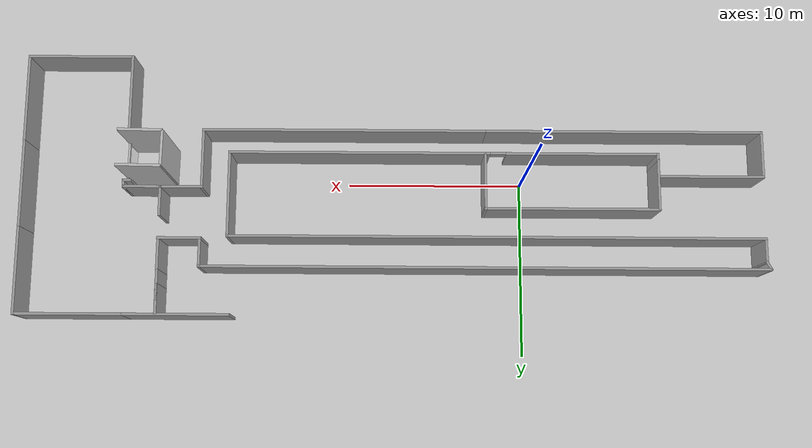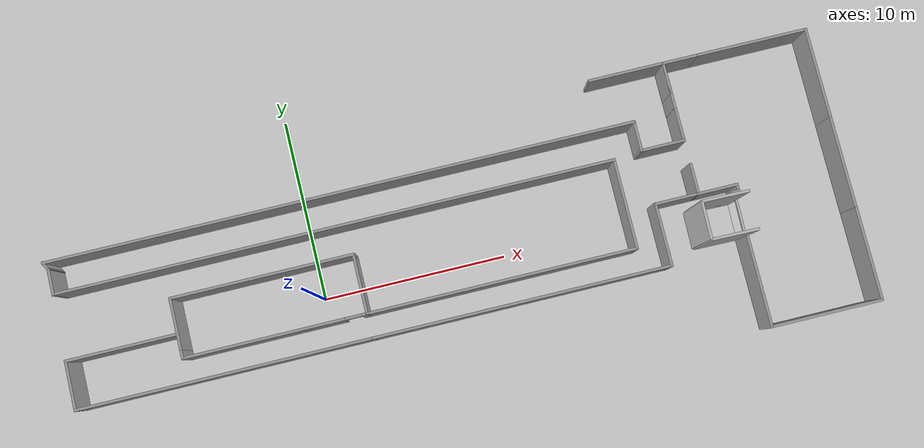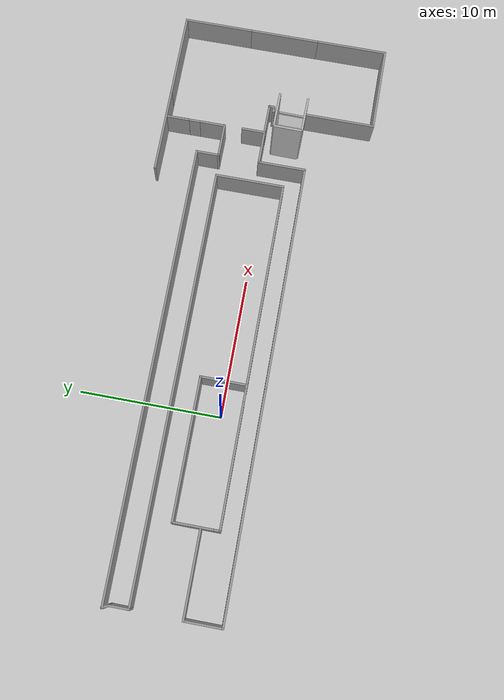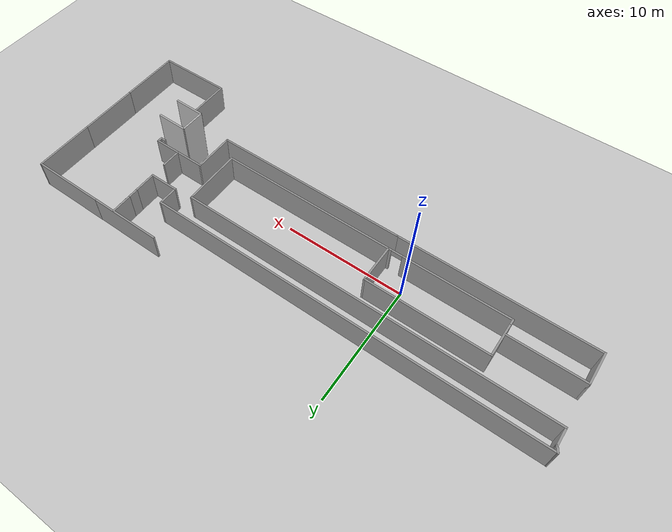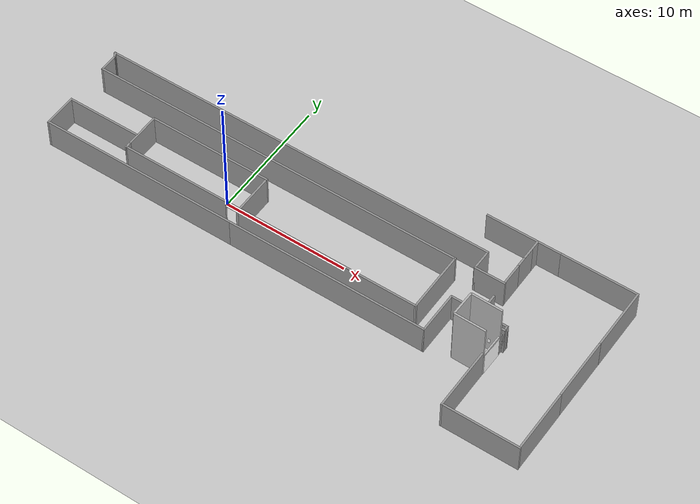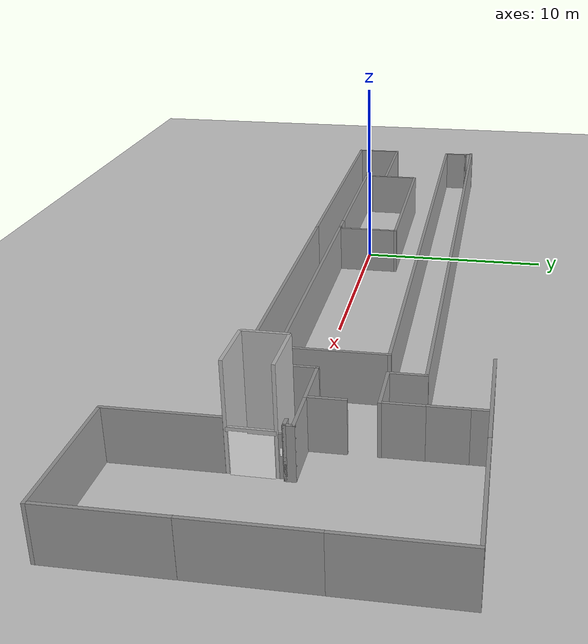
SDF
<sdf version="1.6">
 <world name="default">
  <light name="sun" type="directional">
   <pose>0 0 10 0 -0 0</pose>
   <diffuse>0.8 0.8 0.8 1</diffuse>
   <specular>0.2 0.2 0.2 1</specular>
   <attenuation>
    <range>1000</range>
    <constant>0.9</constant>
    <linear>0.01</linear>
    <quadratic>0.001</quadratic>
   </attenuation>
   <direction>-0.5 0.1 -0.9</direction>
  </light>
  <model name="ground_plane">
   <static>1</static>
   <link name="link">
    <collision name="collision">
     <geometry><plane><normal>0 0 1</normal><size>100 100</size></plane></geometry>
     <surface><friction><ode><mu>100</mu><mu2>50</mu2></ode></friction></surface>
    </collision>
    <visual name="visual">
     <cast_shadows>0</cast_shadows>
     <geometry><plane><normal>0 0 1</normal><size>100 100</size></plane></geometry>
     <material>
      <script><uri>file://media/materials/scripts/gazebo.material</uri><name>Gazebo/Grey</name></script>
     </material>
    </visual>
   </link>
  </model>
  <gravity>0 0 -9.8</gravity>
  <magnetic_field>6e-06 2.3e-05 -4.2e-05</magnetic_field>
  <atmosphere type="adiabatic"/>
  <physics name="default_physics" default="0" type="ode">
   <max_step_size>0.001</max_step_size>
   <real_time_factor>1</real_time_factor>
   <real_time_update_rate>1000</real_time_update_rate>
  </physics>
  <scene><ambient>0.4 0.4 0.4 1</ambient><background>0.7 0.7 0.7 1</background><shadows>1</shadows></scene>
  <spherical_coordinates>
   <surface_model>EARTH_WGS84</surface_model>
   <latitude_deg>0</latitude_deg>
   <longitude_deg>0</longitude_deg>
   <elevation>0</elevation>
   <heading_deg>0</heading_deg>
  </spherical_coordinates>
  <model name="elevator_shaft">
   <link name="elevator_shaft">
    <pose>-1.72355 0.224232 0 0 0 -1.5708</pose>
    <inertial>
     <mass>1</mass>
     <inertia><ixx>1</ixx><ixy>0</ixy><ixz>0</ixz><iyy>1</iyy><iyz>0</iyz><izz>1</izz></inertia>
    </inertial>
    <visual name="shaft_wall3_visual">
     <pose>-1.25 0 2.4774 0 -0 0</pose>
     <geometry><box><size>0.15 2 4.95479</size></box></geometry>
     <material><shader type="pixel"><normal_map>__default__</normal_map></shader></material>
    </visual>
    <visual name="shaft_wall2_visual">
     <pose>0 -1 2.4774 0 -0 0</pose>
     <geometry><box><size>2.5 0.15 4.95479</size></box></geometry>
     <material><shader type="pixel"><normal_map>__default__</normal_map></shader></material>
    </visual>
    <visual name="shaft_wall1_visual">
     <pose>0 1 2.4774 0 -0 0</pose>
     <geometry><box><size>2.5 0.15 4.95479</size></box></geometry>
     <material><shader type="pixel"><normal_map>__default__</normal_map></shader></material>
    </visual>
    <visual name="floor1_visual">
     <pose>1.19 0 2 0 -0 0</pose>
     <geometry><box><size>0.12 2 0.2</size></box></geometry>
     <material><shader type="pixel"><normal_map>__default__</normal_map></shader></material>
    </visual>
    <collision name="floor1_collision">
     <pose>1.19 0 2 0 -0 0</pose>
     <geometry><box><size>0.12 2 0.2</size></box></geometry>
     <surface>
      <friction>
       <ode><mu>1</mu><mu2>1</mu2><fdir1>0 0 0</fdir1><slip1>0</slip1><slip2>0</slip2></ode>
       <torsional>
        <coefficient>1</coefficient>
        <patch_radius>0</patch_radius>
        <surface_radius>0</surface_radius>
        <use_patch_radius>1</use_patch_radius>
        <ode><slip>0</slip></ode>
       </torsional>
      </friction>
      <bounce><restitution_coefficient>0</restitution_coefficient><threshold>1e+06</threshold></bounce>
      <contact>
       <collide_without_contact>0</collide_without_contact>
       <collide_without_contact_bitmask>1</collide_without_contact_bitmask>
       <collide_bitmask>1</collide_bitmask>
       <ode>
        <soft_cfm>0</soft_cfm>
        <soft_erp>0.2</soft_erp>
        <kp>1e+13</kp>
        <kd>1</kd>
        <max_vel>0.01</max_vel>
        <min_depth>0</min_depth>
       </ode>
       <bullet>
        <split_impulse>1</split_impulse>
        <split_impulse_penetration_threshold>-0.01</split_impulse_penetration_threshold>
        <soft_cfm>0</soft_cfm>
        <soft_erp>0.2</soft_erp>
        <kp>1e+13</kp>
        <kd>1</kd>
       </bullet>
      </contact>
     </surface>
    </collision>
    <collision name="shaft_wall3_collision">
     <pose>-1.25 0 2.4774 0 -0 0</pose>
     <geometry><box><size>0.15 2 4.95479</size></box></geometry>
     <surface>
      <friction>
       <ode><mu>1</mu><mu2>1</mu2><fdir1>0 0 0</fdir1><slip1>0</slip1><slip2>0</slip2></ode>
       <torsional>
        <coefficient>1</coefficient>
        <patch_radius>0</patch_radius>
        <surface_radius>0</surface_radius>
        <use_patch_radius>1</use_patch_radius>
        <ode><slip>0</slip></ode>
       </torsional>
      </friction>
      <bounce><restitution_coefficient>0</restitution_coefficient><threshold>1e+06</threshold></bounce>
      <contact>
       <collide_without_contact>0</collide_without_contact>
       <collide_without_contact_bitmask>1</collide_without_contact_bitmask>
       <collide_bitmask>1</collide_bitmask>
       <ode>
        <soft_cfm>0</soft_cfm>
        <soft_erp>0.2</soft_erp>
        <kp>1e+13</kp>
        <kd>1</kd>
        <max_vel>0.01</max_vel>
        <min_depth>0</min_depth>
       </ode>
       <bullet>
        <split_impulse>1</split_impulse>
        <split_impulse_penetration_threshold>-0.01</split_impulse_penetration_threshold>
        <soft_cfm>0</soft_cfm>
        <soft_erp>0.2</soft_erp>
        <kp>1e+13</kp>
        <kd>1</kd>
       </bullet>
      </contact>
     </surface>
    </collision>
    <collision name="shaft_wall2_collision">
     <pose>0 -1 2.4774 0 -0 0</pose>
     <geometry><box><size>2.5 0.15 4.95479</size></box></geometry>
     <surface>
      <friction>
       <ode><mu>1</mu><mu2>1</mu2><fdir1>0 0 0</fdir1><slip1>0</slip1><slip2>0</slip2></ode>
       <torsional>
        <coefficient>1</coefficient>
        <patch_radius>0</patch_radius>
        <surface_radius>0</surface_radius>
        <use_patch_radius>1</use_patch_radius>
        <ode><slip>0</slip></ode>
       </torsional>
      </friction>
      <bounce><restitution_coefficient>0</restitution_coefficient><threshold>1e+06</threshold></bounce>
      <contact>
       <collide_without_contact>0</collide_without_contact>
       <collide_without_contact_bitmask>1</collide_without_contact_bitmask>
       <collide_bitmask>1</collide_bitmask>
       <ode>
        <soft_cfm>0</soft_cfm>
        <soft_erp>0.2</soft_erp>
        <kp>1e+13</kp>
        <kd>1</kd>
        <max_vel>0.01</max_vel>
        <min_depth>0</min_depth>
       </ode>
       <bullet>
        <split_impulse>1</split_impulse>
        <split_impulse_penetration_threshold>-0.01</split_impulse_penetration_threshold>
        <soft_cfm>0</soft_cfm>
        <soft_erp>0.2</soft_erp>
        <kp>1e+13</kp>
        <kd>1</kd>
       </bullet>
      </contact>
     </surface>
    </collision>
    <collision name="shaft_wall1_collision">
     <pose>0 1 2.4774 0 -0 0</pose>
     <geometry><box><size>2.5 0.15 4.95479</size></box></geometry>
     <surface>
      <friction>
       <ode><mu>1</mu><mu2>1</mu2><fdir1>0 0 0</fdir1><slip1>0</slip1><slip2>0</slip2></ode>
       <torsional>
        <coefficient>1</coefficient>
        <patch_radius>0</patch_radius>
        <surface_radius>0</surface_radius>
        <use_patch_radius>1</use_patch_radius>
        <ode><slip>0</slip></ode>
       </torsional>
      </friction>
      <bounce><restitution_coefficient>0</restitution_coefficient><threshold>1e+06</threshold></bounce>
      <contact>
       <collide_without_contact>0</collide_without_contact>
       <collide_without_contact_bitmask>1</collide_without_contact_bitmask>
       <collide_bitmask>1</collide_bitmask>
       <ode>
        <soft_cfm>0</soft_cfm>
        <soft_erp>0.2</soft_erp>
        <kp>1e+13</kp>
        <kd>1</kd>
        <max_vel>0.01</max_vel>
        <min_depth>0</min_depth>
       </ode>
       <bullet>
        <split_impulse>1</split_impulse>
        <split_impulse_penetration_threshold>-0.01</split_impulse_penetration_threshold>
        <soft_cfm>0</soft_cfm>
        <soft_erp>0.2</soft_erp>
        <kp>1e+13</kp>
        <kd>1</kd>
       </bullet>
      </contact>
     </surface>
    </collision>
   </link>
   <link name="buttons_link">
    <pose>-0.5624 -1.03258 1.29659 0 -0 0</pose>
    <inertial>
     <mass>1</mass>
     <inertia>
      <ixx>0.166667</ixx>
      <ixy>0</ixy>
      <ixz>0</ixz>
      <iyy>0.166667</iyy>
      <iyz>0</iyz>
      <izz>0.166667</izz>
     </inertia>
    </inertial>
    <visual name="visual">
     <pose>0 0 -0.08 0 -0 0</pose>
     <geometry><box><size>0.09 0.01 0.36</size></box></geometry>
     <material>
      <script>
       <uri>model://elevator_shaft/materials/scripts</uri>
       <uri>model://elevator_shaft/materials/textures</uri>
       <name>Up_down/Diffuse</name>
      </script>
      <shader type="pixel"><normal_map>__default__</normal_map></shader>
      <ambient>1 1 1 1</ambient>
      <diffuse>1 1 1 1</diffuse>
      <specular>0 0 0 1</specular>
      <emissive>0 0 0 1</emissive>
     </material>
    </visual>
    <collision name="collision">
     <pose>0 0 -0.08 0 -0 0</pose>
     <geometry><box><size>0.09 0.01 0.36</size></box></geometry>
     <surface>
      <friction>
       <ode><mu>1</mu><mu2>1</mu2><fdir1>0 0 0</fdir1><slip1>0</slip1><slip2>0</slip2></ode>
       <torsional>
        <coefficient>1</coefficient>
        <patch_radius>0</patch_radius>
        <surface_radius>0</surface_radius>
        <use_patch_radius>1</use_patch_radius>
        <ode><slip>0</slip></ode>
       </torsional>
      </friction>
      <bounce><restitution_coefficient>0</restitution_coefficient><threshold>1e+06</threshold></bounce>
      <contact>
       <collide_without_contact>0</collide_without_contact>
       <collide_without_contact_bitmask>1</collide_without_contact_bitmask>
       <collide_bitmask>1</collide_bitmask>
       <ode>
        <soft_cfm>0</soft_cfm>
        <soft_erp>0.2</soft_erp>
        <kp>1e+13</kp>
        <kd>1</kd>
        <max_vel>0.01</max_vel>
        <min_depth>0</min_depth>
       </ode>
       <bullet>
        <split_impulse>1</split_impulse>
        <split_impulse_penetration_threshold>-0.01</split_impulse_penetration_threshold>
        <soft_cfm>0</soft_cfm>
        <soft_erp>0.2</soft_erp>
        <kp>1e+13</kp>
        <kd>1</kd>
       </bullet>
      </contact>
     </surface>
    </collision>
   </link>
   <link name="buttons_panel">
    <pose>-0.800245 -0.19994 1.00951 0 -0 0</pose>
    <inertial>
     <mass>1</mass>
     <inertia>
      <ixx>0.166667</ixx>
      <ixy>0</ixy>
      <ixz>0</ixz>
      <iyy>0.166667</iyy>
      <iyz>0</iyz>
      <izz>0.166667</izz>
     </inertia>
     <pose>0 0 0 0 -0 1.57</pose>
    </inertial>
    <visual name="visual">
     <pose>0 0 0 0 -0 1.57</pose>
     <geometry><box><size>0.2 0.01 0.4</size></box></geometry>
     <material>
      <script>
       <uri>model://elevator_shaft/materials/scripts</uri>
       <uri>model://elevator_shaft/materials/textures</uri>
       <name>Buttons_panel/Picture</name>
      </script>
      <shader type="pixel"/>
      <ambient>1 1 1 1</ambient>
      <diffuse>1 1 1 1</diffuse>
      <specular>0 0 0 1</specular>
      <emissive>0 0 0 1</emissive>
     </material>
    </visual>
    <collision name="collision">
     <pose>0 0 0 0 -0 1.57</pose>
     <geometry><box><size>0.05 0.01 0.1</size></box></geometry>
     <surface>
      <friction>
       <ode><mu>1</mu><mu2>1</mu2><fdir1>0 0 0</fdir1><slip1>0</slip1><slip2>0</slip2></ode>
       <torsional>
        <coefficient>1</coefficient>
        <patch_radius>0</patch_radius>
        <surface_radius>0</surface_radius>
        <use_patch_radius>1</use_patch_radius>
        <ode><slip>0</slip></ode>
       </torsional>
      </friction>
      <bounce><restitution_coefficient>0</restitution_coefficient><threshold>1e+06</threshold></bounce>
      <contact>
       <collide_without_contact>0</collide_without_contact>
       <collide_without_contact_bitmask>1</collide_without_contact_bitmask>
       <collide_bitmask>1</collide_bitmask>
       <ode>
        <soft_cfm>0</soft_cfm>
        <soft_erp>0.2</soft_erp>
        <kp>1e+13</kp>
        <kd>1</kd>
        <max_vel>0.01</max_vel>
        <min_depth>0</min_depth>
       </ode>
       <bullet>
        <split_impulse>1</split_impulse>
        <split_impulse_penetration_threshold>-0.01</split_impulse_penetration_threshold>
        <soft_cfm>0</soft_cfm>
        <soft_erp>0.2</soft_erp>
        <kp>1e+13</kp>
        <kd>1</kd>
       </bullet>
      </contact>
     </surface>
    </collision>
   </link>
   <link name="link_0">
    <pose>-0.562882 -0.977907 1.0001 0 -0 0</pose>
    <inertial>
     <mass>1</mass>
     <inertia>
      <ixx>0.166667</ixx>
      <ixy>0</ixy>
      <ixz>0</ixz>
      <iyy>0.166667</iyy>
      <iyz>0</iyz>
      <izz>0.166667</izz>
     </inertia>
    </inertial>
    <visual name="visual">
     <geometry><box><size>0.2 0.1 2</size></box></geometry>
     <material>
      <lighting>1</lighting>
      <script><uri>file://media/materials/scripts/gazebo.material</uri><name>Gazebo/Grey</name></script>
      <shader type="pixel"><normal_map>__default__</normal_map></shader>
      <ambient>0.3 0.3 0.3 1</ambient>
      <diffuse>0.7 0.7 0.7 1</diffuse>
      <specular>0.01 0.01 0.01 1</specular>
      <emissive>0 0 0 1</emissive>
     </material>
    </visual>
    <collision name="collision">
     <geometry><box><size>0.2 0.1 2</size></box></geometry>
     <surface>
      <friction>
       <ode><mu>1</mu><mu2>1</mu2><fdir1>0 0 0</fdir1><slip1>0</slip1><slip2>0</slip2></ode>
       <torsional>
        <coefficient>1</coefficient>
        <patch_radius>0</patch_radius>
        <surface_radius>0</surface_radius>
        <use_patch_radius>1</use_patch_radius>
        <ode><slip>0</slip></ode>
       </torsional>
      </friction>
      <bounce><restitution_coefficient>0</restitution_coefficient><threshold>1e+06</threshold></bounce>
      <contact>
       <collide_without_contact>0</collide_without_contact>
       <collide_without_contact_bitmask>1</collide_without_contact_bitmask>
       <collide_bitmask>1</collide_bitmask>
       <ode>
        <soft_cfm>0</soft_cfm>
        <soft_erp>0.2</soft_erp>
        <kp>1e+13</kp>
        <kd>1</kd>
        <max_vel>0.01</max_vel>
        <min_depth>0</min_depth>
       </ode>
       <bullet>
        <split_impulse>1</split_impulse>
        <split_impulse_penetration_threshold>-0.01</split_impulse_penetration_threshold>
        <soft_cfm>0</soft_cfm>
        <soft_erp>0.2</soft_erp>
        <kp>1e+13</kp>
        <kd>1</kd>
       </bullet>
      </contact>
     </surface>
    </collision>
   </link>
   <static>1</static>
   <pose>21.6684 0.69961 0 0 -0 1.55499</pose>
  </model>
  <model name="elevator_door">
   <link name="link">
    <pose>0.086726 -0.429033 0.450416 0 -0 0</pose>
    <inertial>
     <mass>1</mass>
     <inertia>
      <ixx>0.166667</ixx>
      <ixy>0</ixy>
      <ixz>0</ixz>
      <iyy>0.166667</iyy>
      <iyz>0</iyz>
      <izz>0.166667</izz>
     </inertia>
     <pose>0 0 0.5 0 -0 0</pose>
    </inertial>
    <visual name="visual">
     <geometry><box><size>1.8 0.05 2</size></box></geometry>
     <material>
      <script>
       <uri>model://elevator_door/materials/scripts</uri>
       <uri>model://elevator_door/materials/textures</uri>
       <name>Elevator_door/Picture</name>
      </script>
      <shader type="pixel"><normal_map>__default__</normal_map></shader>
      <ambient>1 1 1 1</ambient>
      <diffuse>1 1 1 1</diffuse>
      <specular>0 0 0 1</specular>
      <emissive>0 0 0 1</emissive>
     </material>
     <pose>0 0 0.5 0 -0 0</pose>
    </visual>
    <collision name="collision">
     <pose>0 0 0.5 0 -0 0</pose>
     <geometry><box><size>1.8 0.05 2</size></box></geometry>
     <surface>
      <friction>
       <ode><mu>1</mu><mu2>1</mu2><fdir1>0 0 0</fdir1><slip1>0</slip1><slip2>0</slip2></ode>
       <torsional>
        <coefficient>1</coefficient>
        <patch_radius>0</patch_radius>
        <surface_radius>0</surface_radius>
        <use_patch_radius>1</use_patch_radius>
        <ode><slip>0</slip></ode>
       </torsional>
      </friction>
      <bounce><restitution_coefficient>0</restitution_coefficient><threshold>1e+06</threshold></bounce>
      <contact>
       <collide_without_contact>0</collide_without_contact>
       <collide_without_contact_bitmask>1</collide_without_contact_bitmask>
       <collide_bitmask>1</collide_bitmask>
       <ode>
        <soft_cfm>0</soft_cfm>
        <soft_erp>0.2</soft_erp>
        <kp>1e+13</kp>
        <kd>1</kd>
        <max_vel>0.01</max_vel>
        <min_depth>0</min_depth>
       </ode>
       <bullet>
        <split_impulse>1</split_impulse>
        <split_impulse_penetration_threshold>-0.01</split_impulse_penetration_threshold>
        <soft_cfm>0</soft_cfm>
        <soft_erp>0.2</soft_erp>
        <kp>1e+13</kp>
        <kd>1</kd>
       </bullet>
      </contact>
     </surface>
    </collision>
   </link>
   <static>1</static>
   <pose>23.0715 -0.950449 0 0 0 -1.58296</pose>
  </model>
  <model name="Untitled">
   <link name="Wall_20">
    <pose>-2.30407 -1.00044 0 0 -0 1.5708</pose>
    <visual name="Wall_20_Visual">
     <pose>0 0 1.25 0 -0 0</pose>
     <geometry><box><size>3.25 0.15 2.5</size></box></geometry>
     <material>
      <script><uri>file://media/materials/scripts/gazebo.material</uri><name>Gazebo/Grey</name></script>
      <ambient>1 1 1 1</ambient>
      <shader type="pixel"/>
      <diffuse>0.7 0.7 0.7 1</diffuse>
      <specular>0.01 0.01 0.01 1</specular>
      <emissive>0 0 0 1</emissive>
     </material>
     <meta><layer>0</layer></meta>
    </visual>
    <collision name="Wall_20_Collision">
     <pose>0 0 1.25 0 -0 0</pose>
     <geometry><box><size>3.25 0.15 2.5</size></box></geometry>
     <surface>
      <friction>
       <ode><mu>1</mu><mu2>1</mu2><fdir1>0 0 0</fdir1><slip1>0</slip1><slip2>0</slip2></ode>
       <torsional>
        <coefficient>1</coefficient>
        <patch_radius>0</patch_radius>
        <surface_radius>0</surface_radius>
        <use_patch_radius>1</use_patch_radius>
        <ode><slip>0</slip></ode>
       </torsional>
      </friction>
      <bounce><restitution_coefficient>0</restitution_coefficient><threshold>1e+06</threshold></bounce>
      <contact>
       <collide_without_contact>0</collide_without_contact>
       <collide_without_contact_bitmask>1</collide_without_contact_bitmask>
       <collide_bitmask>1</collide_bitmask>
       <ode>
        <soft_cfm>0</soft_cfm>
        <soft_erp>0.2</soft_erp>
        <kp>1e+13</kp>
        <kd>1</kd>
        <max_vel>0.01</max_vel>
        <min_depth>0</min_depth>
       </ode>
       <bullet>
        <split_impulse>1</split_impulse>
        <split_impulse_penetration_threshold>-0.01</split_impulse_penetration_threshold>
        <soft_cfm>0</soft_cfm>
        <soft_erp>0.2</soft_erp>
        <kp>1e+13</kp>
        <kd>1</kd>
       </bullet>
      </contact>
     </surface>
    </collision>
   </link>
   <link name="Wall_21">
    <pose>-7.22907 0.549559 0 0 -0 3.14159</pose>
    <visual name="Wall_21_Visual">
     <pose>0 0 1.25 0 -0 0</pose>
     <geometry><box><size>10 0.15 2.5</size></box></geometry>
     <material>
      <script><uri>file://media/materials/scripts/gazebo.material</uri><name>Gazebo/Grey</name></script>
      <ambient>1 1 1 1</ambient>
      <shader type="pixel"/>
      <diffuse>0.7 0.7 0.7 1</diffuse>
      <specular>0.01 0.01 0.01 1</specular>
      <emissive>0 0 0 1</emissive>
     </material>
     <meta><layer>0</layer></meta>
    </visual>
    <collision name="Wall_21_Collision">
     <pose>0 0 1.25 0 -0 0</pose>
     <geometry><box><size>10 0.15 2.5</size></box></geometry>
     <surface>
      <friction>
       <ode><mu>1</mu><mu2>1</mu2><fdir1>0 0 0</fdir1><slip1>0</slip1><slip2>0</slip2></ode>
       <torsional>
        <coefficient>1</coefficient>
        <patch_radius>0</patch_radius>
        <surface_radius>0</surface_radius>
        <use_patch_radius>1</use_patch_radius>
        <ode><slip>0</slip></ode>
       </torsional>
      </friction>
      <bounce><restitution_coefficient>0</restitution_coefficient><threshold>1e+06</threshold></bounce>
      <contact>
       <collide_without_contact>0</collide_without_contact>
       <collide_without_contact_bitmask>1</collide_without_contact_bitmask>
       <collide_bitmask>1</collide_bitmask>
       <ode>
        <soft_cfm>0</soft_cfm>
        <soft_erp>0.2</soft_erp>
        <kp>1e+13</kp>
        <kd>1</kd>
        <max_vel>0.01</max_vel>
        <min_depth>0</min_depth>
       </ode>
       <bullet>
        <split_impulse>1</split_impulse>
        <split_impulse_penetration_threshold>-0.01</split_impulse_penetration_threshold>
        <soft_cfm>0</soft_cfm>
        <soft_erp>0.2</soft_erp>
        <kp>1e+13</kp>
        <kd>1</kd>
       </bullet>
      </contact>
     </surface>
    </collision>
   </link>
   <link name="Wall_22">
    <pose>-12.1541 -0.875442 0 0 0 -1.5708</pose>
    <visual name="Wall_22_Visual">
     <pose>0 0 1.25 0 -0 0</pose>
     <geometry><box><size>3 0.15 2.5</size></box></geometry>
     <material>
      <script><uri>file://media/materials/scripts/gazebo.material</uri><name>Gazebo/Grey</name></script>
      <ambient>1 1 1 1</ambient>
      <shader type="pixel"/>
      <diffuse>0.7 0.7 0.7 1</diffuse>
      <specular>0.01 0.01 0.01 1</specular>
      <emissive>0 0 0 1</emissive>
     </material>
     <meta><layer>0</layer></meta>
    </visual>
    <collision name="Wall_22_Collision">
     <pose>0 0 1.25 0 -0 0</pose>
     <geometry><box><size>3 0.15 2.5</size></box></geometry>
     <surface>
      <friction>
       <ode><mu>1</mu><mu2>1</mu2><fdir1>0 0 0</fdir1><slip1>0</slip1><slip2>0</slip2></ode>
       <torsional>
        <coefficient>1</coefficient>
        <patch_radius>0</patch_radius>
        <surface_radius>0</surface_radius>
        <use_patch_radius>1</use_patch_radius>
        <ode><slip>0</slip></ode>
       </torsional>
      </friction>
      <bounce><restitution_coefficient>0</restitution_coefficient><threshold>1e+06</threshold></bounce>
      <contact>
       <collide_without_contact>0</collide_without_contact>
       <collide_without_contact_bitmask>1</collide_without_contact_bitmask>
       <collide_bitmask>1</collide_bitmask>
       <ode>
        <soft_cfm>0</soft_cfm>
        <soft_erp>0.2</soft_erp>
        <kp>1e+13</kp>
        <kd>1</kd>
        <max_vel>0.01</max_vel>
        <min_depth>0</min_depth>
       </ode>
       <bullet>
        <split_impulse>1</split_impulse>
        <split_impulse_penetration_threshold>-0.01</split_impulse_penetration_threshold>
        <soft_cfm>0</soft_cfm>
        <soft_erp>0.2</soft_erp>
        <kp>1e+13</kp>
        <kd>1</kd>
       </bullet>
      </contact>
     </surface>
    </collision>
   </link>
   <link name="Wall_23">
    <pose>-12.1541 -2.47544 0 0 0 -1.5708</pose>
    <visual name="Wall_23_Visual">
     <pose>0 0 1.25 0 -0 0</pose>
     <geometry><box><size>0.5 0.15 2.5</size></box></geometry>
     <material>
      <script><uri>file://media/materials/scripts/gazebo.material</uri><name>Gazebo/Grey</name></script>
      <ambient>1 1 1 1</ambient>
      <shader type="pixel"/>
      <diffuse>0.7 0.7 0.7 1</diffuse>
      <specular>0.01 0.01 0.01 1</specular>
      <emissive>0 0 0 1</emissive>
     </material>
     <meta><layer>0</layer></meta>
    </visual>
    <collision name="Wall_23_Collision">
     <pose>0 0 1.25 0 -0 0</pose>
     <geometry><box><size>0.5 0.15 2.5</size></box></geometry>
     <surface>
      <friction>
       <ode><mu>1</mu><mu2>1</mu2><fdir1>0 0 0</fdir1><slip1>0</slip1><slip2>0</slip2></ode>
       <torsional>
        <coefficient>1</coefficient>
        <patch_radius>0</patch_radius>
        <surface_radius>0</surface_radius>
        <use_patch_radius>1</use_patch_radius>
        <ode><slip>0</slip></ode>
       </torsional>
      </friction>
      <bounce><restitution_coefficient>0</restitution_coefficient><threshold>1e+06</threshold></bounce>
      <contact>
       <collide_without_contact>0</collide_without_contact>
       <collide_without_contact_bitmask>1</collide_without_contact_bitmask>
       <collide_bitmask>1</collide_bitmask>
       <ode>
        <soft_cfm>0</soft_cfm>
        <soft_erp>0.2</soft_erp>
        <kp>1e+13</kp>
        <kd>1</kd>
        <max_vel>0.01</max_vel>
        <min_depth>0</min_depth>
       </ode>
       <bullet>
        <split_impulse>1</split_impulse>
        <split_impulse_penetration_threshold>-0.01</split_impulse_penetration_threshold>
        <soft_cfm>0</soft_cfm>
        <soft_erp>0.2</soft_erp>
        <kp>1e+13</kp>
        <kd>1</kd>
       </bullet>
      </contact>
     </surface>
    </collision>
   </link>
   <link name="Wall_24">
    <pose>-7.22907 -2.65044 0 0 -0 0</pose>
    <visual name="Wall_24_Visual_1">
     <pose>4.82444 0 1.25 0 -0 0</pose>
     <geometry><box><size>0.351111 0.15 2.5</size></box></geometry>
     <material>
      <script><uri>file://media/materials/scripts/gazebo.material</uri><name>Gazebo/Grey</name></script>
      <ambient>1 1 1 1</ambient>
      <shader type="pixel"/>
      <diffuse>0.7 0.7 0.7 1</diffuse>
      <specular>0.01 0.01 0.01 1</specular>
      <emissive>0 0 0 1</emissive>
     </material>
     <meta><layer>0</layer></meta>
    </visual>
    <visual name="Wall_24_Visual_2">
     <pose>4.19889 0 2.25 0 -0 0</pose>
     <geometry><box><size>0.9 0.15 0.5</size></box></geometry>
     <material>
      <script><uri>file://media/materials/scripts/gazebo.material</uri><name>Gazebo/Grey</name></script>
      <ambient>1 1 1 1</ambient>
      <shader type="pixel"/>
      <diffuse>0.7 0.7 0.7 1</diffuse>
      <specular>0.01 0.01 0.01 1</specular>
      <emissive>0 0 0 1</emissive>
     </material>
     <meta><layer>0</layer></meta>
    </visual>
    <visual name="Wall_24_Visual_0">
     <pose>-0.625555 0 1.25 0 -0 0</pose>
     <geometry><box><size>8.74889 0.15 2.5</size></box></geometry>
     <material>
      <script><uri>file://media/materials/scripts/gazebo.material</uri><name>Gazebo/Grey</name></script>
      <ambient>1 1 1 1</ambient>
      <shader type="pixel"/>
      <diffuse>0.7 0.7 0.7 1</diffuse>
      <specular>0.01 0.01 0.01 1</specular>
      <emissive>0 0 0 1</emissive>
     </material>
     <meta><layer>0</layer></meta>
    </visual>
    <collision name="Wall_24_Collision_2">
     <pose>4.19889 0 2.25 0 -0 0</pose>
     <geometry><box><size>0.9 0.15 0.5</size></box></geometry>
     <surface>
      <friction>
       <ode><mu>1</mu><mu2>1</mu2><fdir1>0 0 0</fdir1><slip1>0</slip1><slip2>0</slip2></ode>
       <torsional>
        <coefficient>1</coefficient>
        <patch_radius>0</patch_radius>
        <surface_radius>0</surface_radius>
        <use_patch_radius>1</use_patch_radius>
        <ode><slip>0</slip></ode>
       </torsional>
      </friction>
      <bounce><restitution_coefficient>0</restitution_coefficient><threshold>1e+06</threshold></bounce>
      <contact>
       <collide_without_contact>0</collide_without_contact>
       <collide_without_contact_bitmask>1</collide_without_contact_bitmask>
       <collide_bitmask>1</collide_bitmask>
       <ode>
        <soft_cfm>0</soft_cfm>
        <soft_erp>0.2</soft_erp>
        <kp>1e+13</kp>
        <kd>1</kd>
        <max_vel>0.01</max_vel>
        <min_depth>0</min_depth>
       </ode>
       <bullet>
        <split_impulse>1</split_impulse>
        <split_impulse_penetration_threshold>-0.01</split_impulse_penetration_threshold>
        <soft_cfm>0</soft_cfm>
        <soft_erp>0.2</soft_erp>
        <kp>1e+13</kp>
        <kd>1</kd>
       </bullet>
      </contact>
     </surface>
    </collision>
    <collision name="Wall_24_Collision_0">
     <pose>-0.625555 0 1.25 0 -0 0</pose>
     <geometry><box><size>8.74889 0.15 2.5</size></box></geometry>
     <surface>
      <friction>
       <ode><mu>1</mu><mu2>1</mu2><fdir1>0 0 0</fdir1><slip1>0</slip1><slip2>0</slip2></ode>
       <torsional>
        <coefficient>1</coefficient>
        <patch_radius>0</patch_radius>
        <surface_radius>0</surface_radius>
        <use_patch_radius>1</use_patch_radius>
        <ode><slip>0</slip></ode>
       </torsional>
      </friction>
      <bounce><restitution_coefficient>0</restitution_coefficient><threshold>1e+06</threshold></bounce>
      <contact>
       <collide_without_contact>0</collide_without_contact>
       <collide_without_contact_bitmask>1</collide_without_contact_bitmask>
       <collide_bitmask>1</collide_bitmask>
       <ode>
        <soft_cfm>0</soft_cfm>
        <soft_erp>0.2</soft_erp>
        <kp>1e+13</kp>
        <kd>1</kd>
        <max_vel>0.01</max_vel>
        <min_depth>0</min_depth>
       </ode>
       <bullet>
        <split_impulse>1</split_impulse>
        <split_impulse_penetration_threshold>-0.01</split_impulse_penetration_threshold>
        <soft_cfm>0</soft_cfm>
        <soft_erp>0.2</soft_erp>
        <kp>1e+13</kp>
        <kd>1</kd>
       </bullet>
      </contact>
     </surface>
    </collision>
    <collision name="Wall_24_Collision_1">
     <pose>4.82444 0 1.25 0 -0 0</pose>
     <geometry><box><size>0.351111 0.15 2.5</size></box></geometry>
     <surface>
      <friction>
       <ode><mu>1</mu><mu2>1</mu2><fdir1>0 0 0</fdir1><slip1>0</slip1><slip2>0</slip2></ode>
       <torsional>
        <coefficient>1</coefficient>
        <patch_radius>0</patch_radius>
        <surface_radius>0</surface_radius>
        <use_patch_radius>1</use_patch_radius>
        <ode><slip>0</slip></ode>
       </torsional>
      </friction>
      <bounce><restitution_coefficient>0</restitution_coefficient><threshold>1e+06</threshold></bounce>
      <contact>
       <collide_without_contact>0</collide_without_contact>
       <collide_without_contact_bitmask>1</collide_without_contact_bitmask>
       <collide_bitmask>1</collide_bitmask>
       <ode>
        <soft_cfm>0</soft_cfm>
        <soft_erp>0.2</soft_erp>
        <kp>1e+13</kp>
        <kd>1</kd>
        <max_vel>0.01</max_vel>
        <min_depth>0</min_depth>
       </ode>
       <bullet>
        <split_impulse>1</split_impulse>
        <split_impulse_penetration_threshold>-0.01</split_impulse_penetration_threshold>
        <soft_cfm>0</soft_cfm>
        <soft_erp>0.2</soft_erp>
        <kp>1e+13</kp>
        <kd>1</kd>
       </bullet>
      </contact>
     </surface>
    </collision>
   </link>
   <link name="Wall_28">
    <pose>-10.1867 -3.96327 0 0 -0 3.14159</pose>
    <visual name="Wall_28_Visual">
     <pose>0 0 1.25 0 -0 0</pose>
     <geometry><box><size>16 0.15 2.5</size></box></geometry>
     <material>
      <script><uri>file://media/materials/scripts/gazebo.material</uri><name>Gazebo/Grey</name></script>
      <ambient>1 1 1 1</ambient>
      <shader type="pixel"/>
      <diffuse>0.7 0.7 0.7 1</diffuse>
      <specular>0.01 0.01 0.01 1</specular>
      <emissive>0 0 0 1</emissive>
     </material>
     <meta><layer>0</layer></meta>
    </visual>
    <collision name="Wall_28_Collision">
     <pose>0 0 1.25 0 -0 0</pose>
     <geometry><box><size>16 0.15 2.5</size></box></geometry>
     <surface>
      <friction>
       <ode><mu>1</mu><mu2>1</mu2><fdir1>0 0 0</fdir1><slip1>0</slip1><slip2>0</slip2></ode>
       <torsional>
        <coefficient>1</coefficient>
        <patch_radius>0</patch_radius>
        <surface_radius>0</surface_radius>
        <use_patch_radius>1</use_patch_radius>
        <ode><slip>0</slip></ode>
       </torsional>
      </friction>
      <bounce><restitution_coefficient>0</restitution_coefficient><threshold>1e+06</threshold></bounce>
      <contact>
       <collide_without_contact>0</collide_without_contact>
       <collide_without_contact_bitmask>1</collide_without_contact_bitmask>
       <collide_bitmask>1</collide_bitmask>
       <ode>
        <soft_cfm>0</soft_cfm>
        <soft_erp>0.2</soft_erp>
        <kp>1e+13</kp>
        <kd>1</kd>
        <max_vel>0.01</max_vel>
        <min_depth>0</min_depth>
       </ode>
       <bullet>
        <split_impulse>1</split_impulse>
        <split_impulse_penetration_threshold>-0.01</split_impulse_penetration_threshold>
        <soft_cfm>0</soft_cfm>
        <soft_erp>0.2</soft_erp>
        <kp>1e+13</kp>
        <kd>1</kd>
       </bullet>
      </contact>
     </surface>
    </collision>
   </link>
   <link name="Wall_29">
    <pose>-18.1117 -2.66327 0 0 -0 1.5708</pose>
    <visual name="Wall_29_Visual">
     <pose>0 0 1.25 0 -0 0</pose>
     <geometry><box><size>2.75 0.15 2.5</size></box></geometry>
     <material>
      <script><uri>file://media/materials/scripts/gazebo.material</uri><name>Gazebo/Grey</name></script>
      <ambient>1 1 1 1</ambient>
      <shader type="pixel"/>
      <diffuse>0.7 0.7 0.7 1</diffuse>
      <specular>0.01 0.01 0.01 1</specular>
      <emissive>0 0 0 1</emissive>
     </material>
     <meta><layer>0</layer></meta>
    </visual>
    <collision name="Wall_29_Collision">
     <pose>0 0 1.25 0 -0 0</pose>
     <geometry><box><size>2.75 0.15 2.5</size></box></geometry>
     <surface>
      <friction>
       <ode><mu>1</mu><mu2>1</mu2><fdir1>0 0 0</fdir1><slip1>0</slip1><slip2>0</slip2></ode>
       <torsional>
        <coefficient>1</coefficient>
        <patch_radius>0</patch_radius>
        <surface_radius>0</surface_radius>
        <use_patch_radius>1</use_patch_radius>
        <ode><slip>0</slip></ode>
       </torsional>
      </friction>
      <bounce><restitution_coefficient>0</restitution_coefficient><threshold>1e+06</threshold></bounce>
      <contact>
       <collide_without_contact>0</collide_without_contact>
       <collide_without_contact_bitmask>1</collide_without_contact_bitmask>
       <collide_bitmask>1</collide_bitmask>
       <ode>
        <soft_cfm>0</soft_cfm>
        <soft_erp>0.2</soft_erp>
        <kp>1e+13</kp>
        <kd>1</kd>
        <max_vel>0.01</max_vel>
        <min_depth>0</min_depth>
       </ode>
       <bullet>
        <split_impulse>1</split_impulse>
        <split_impulse_penetration_threshold>-0.01</split_impulse_penetration_threshold>
        <soft_cfm>0</soft_cfm>
        <soft_erp>0.2</soft_erp>
        <kp>1e+13</kp>
        <kd>1</kd>
       </bullet>
      </contact>
     </surface>
    </collision>
   </link>
   <link name="Wall_30">
    <pose>-15.1867 -1.36327 0 0 -0 0</pose>
    <visual name="Wall_30_Visual">
     <pose>0 0 1.25 0 -0 0</pose>
     <geometry><box><size>6 0.15 2.5</size></box></geometry>
     <material>
      <script><uri>file://media/materials/scripts/gazebo.material</uri><name>Gazebo/Grey</name></script>
      <ambient>1 1 1 1</ambient>
      <shader type="pixel"/>
      <diffuse>0.7 0.7 0.7 1</diffuse>
      <specular>0.01 0.01 0.01 1</specular>
      <emissive>0 0 0 1</emissive>
     </material>
     <meta><layer>0</layer></meta>
    </visual>
    <collision name="Wall_30_Collision">
     <pose>0 0 1.25 0 -0 0</pose>
     <geometry><box><size>6 0.15 2.5</size></box></geometry>
     <surface>
      <friction>
       <ode><mu>1</mu><mu2>1</mu2><fdir1>0 0 0</fdir1><slip1>0</slip1><slip2>0</slip2></ode>
       <torsional>
        <coefficient>1</coefficient>
        <patch_radius>0</patch_radius>
        <surface_radius>0</surface_radius>
        <use_patch_radius>1</use_patch_radius>
        <ode><slip>0</slip></ode>
       </torsional>
      </friction>
      <bounce><restitution_coefficient>0</restitution_coefficient><threshold>1e+06</threshold></bounce>
      <contact>
       <collide_without_contact>0</collide_without_contact>
       <collide_without_contact_bitmask>1</collide_without_contact_bitmask>
       <collide_bitmask>1</collide_bitmask>
       <ode>
        <soft_cfm>0</soft_cfm>
        <soft_erp>0.2</soft_erp>
        <kp>1e+13</kp>
        <kd>1</kd>
        <max_vel>0.01</max_vel>
        <min_depth>0</min_depth>
       </ode>
       <bullet>
        <split_impulse>1</split_impulse>
        <split_impulse_penetration_threshold>-0.01</split_impulse_penetration_threshold>
        <soft_cfm>0</soft_cfm>
        <soft_erp>0.2</soft_erp>
        <kp>1e+13</kp>
        <kd>1</kd>
       </bullet>
      </contact>
     </surface>
    </collision>
   </link>
   <link name="Wall_30_clone">
    <pose>21.1612 -8.29144 0 0 -0 0</pose>
    <visual name="Wall_30_Visual">
     <pose>0 0 1.25 0 -0 0</pose>
     <geometry><box><size>6 0.15 2.5</size></box></geometry>
     <material>
      <script><uri>file://media/materials/scripts/gazebo.material</uri><name>Gazebo/Grey</name></script>
      <ambient>1 1 1 1</ambient>
      <shader type="pixel"/>
      <diffuse>0.7 0.7 0.7 1</diffuse>
      <specular>0.01 0.01 0.01 1</specular>
      <emissive>0 0 0 1</emissive>
     </material>
     <meta><layer>0</layer></meta>
    </visual>
    <collision name="Wall_30_Collision">
     <pose>0 0 1.25 0 -0 0</pose>
     <geometry><box><size>6 0.15 2.5</size></box></geometry>
     <surface>
      <friction>
       <ode><mu>1</mu><mu2>1</mu2><fdir1>0 0 0</fdir1><slip1>0</slip1><slip2>0</slip2></ode>
       <torsional>
        <coefficient>1</coefficient>
        <patch_radius>0</patch_radius>
        <surface_radius>0</surface_radius>
        <use_patch_radius>1</use_patch_radius>
        <ode><slip>0</slip></ode>
       </torsional>
      </friction>
      <bounce><restitution_coefficient>0</restitution_coefficient><threshold>1e+06</threshold></bounce>
      <contact>
       <collide_without_contact>0</collide_without_contact>
       <collide_without_contact_bitmask>1</collide_without_contact_bitmask>
       <collide_bitmask>1</collide_bitmask>
       <ode>
        <soft_cfm>0</soft_cfm>
        <soft_erp>0.2</soft_erp>
        <kp>1e+13</kp>
        <kd>1</kd>
        <max_vel>0.01</max_vel>
        <min_depth>0</min_depth>
       </ode>
       <bullet>
        <split_impulse>1</split_impulse>
        <split_impulse_penetration_threshold>-0.01</split_impulse_penetration_threshold>
        <soft_cfm>0</soft_cfm>
        <soft_erp>0.2</soft_erp>
        <kp>1e+13</kp>
        <kd>1</kd>
       </bullet>
      </contact>
     </surface>
    </collision>
   </link>
   <link name="Wall_30_clone_clone">
    <pose>21.0171 6.65699 0 0 -0 0</pose>
    <visual name="Wall_30_Visual">
     <pose>0 0 1.25 0 -0 0</pose>
     <geometry><box><size>6 0.15 2.5</size></box></geometry>
     <material>
      <script><uri>file://media/materials/scripts/gazebo.material</uri><name>Gazebo/Grey</name></script>
      <ambient>1 1 1 1</ambient>
      <shader type="pixel"/>
      <diffuse>0.7 0.7 0.7 1</diffuse>
      <specular>0.01 0.01 0.01 1</specular>
      <emissive>0 0 0 1</emissive>
     </material>
     <meta><layer>0</layer></meta>
    </visual>
    <collision name="Wall_30_Collision">
     <pose>0 0 1.25 0 -0 0</pose>
     <geometry><box><size>6 0.15 2.5</size></box></geometry>
     <surface>
      <friction>
       <ode><mu>1</mu><mu2>1</mu2><fdir1>0 0 0</fdir1><slip1>0</slip1><slip2>0</slip2></ode>
       <torsional>
        <coefficient>1</coefficient>
        <patch_radius>0</patch_radius>
        <surface_radius>0</surface_radius>
        <use_patch_radius>1</use_patch_radius>
        <ode><slip>0</slip></ode>
       </torsional>
      </friction>
      <bounce><restitution_coefficient>0</restitution_coefficient><threshold>1e+06</threshold></bounce>
      <contact>
       <collide_without_contact>0</collide_without_contact>
       <collide_without_contact_bitmask>1</collide_without_contact_bitmask>
       <collide_bitmask>1</collide_bitmask>
       <ode>
        <soft_cfm>0</soft_cfm>
        <soft_erp>0.2</soft_erp>
        <kp>1e+13</kp>
        <kd>1</kd>
        <max_vel>0.01</max_vel>
        <min_depth>0</min_depth>
       </ode>
       <bullet>
        <split_impulse>1</split_impulse>
        <split_impulse_penetration_threshold>-0.01</split_impulse_penetration_threshold>
        <soft_cfm>0</soft_cfm>
        <soft_erp>0.2</soft_erp>
        <kp>1e+13</kp>
        <kd>1</kd>
       </bullet>
      </contact>
     </surface>
    </collision>
   </link>
   <link name="Wall_30_clone_clone_0">
    <pose>15.0202 6.65284 0 0 -0 0</pose>
    <visual name="Wall_30_Visual">
     <pose>0 0 1.25 0 -0 0</pose>
     <geometry><box><size>6 0.15 2.5</size></box></geometry>
     <material>
      <script><uri>file://media/materials/scripts/gazebo.material</uri><name>Gazebo/Grey</name></script>
      <ambient>1 1 1 1</ambient>
      <shader type="pixel"/>
      <diffuse>0.7 0.7 0.7 1</diffuse>
      <specular>0.01 0.01 0.01 1</specular>
      <emissive>0 0 0 1</emissive>
     </material>
     <meta><layer>0</layer></meta>
    </visual>
    <collision name="Wall_30_Collision">
     <pose>0 0 1.25 0 -0 0</pose>
     <geometry><box><size>6 0.15 2.5</size></box></geometry>
     <surface>
      <friction>
       <ode><mu>1</mu><mu2>1</mu2><fdir1>0 0 0</fdir1><slip1>0</slip1><slip2>0</slip2></ode>
       <torsional>
        <coefficient>1</coefficient>
        <patch_radius>0</patch_radius>
        <surface_radius>0</surface_radius>
        <use_patch_radius>1</use_patch_radius>
        <ode><slip>0</slip></ode>
       </torsional>
      </friction>
      <bounce><restitution_coefficient>0</restitution_coefficient><threshold>1e+06</threshold></bounce>
      <contact>
       <collide_without_contact>0</collide_without_contact>
       <collide_without_contact_bitmask>1</collide_without_contact_bitmask>
       <collide_bitmask>1</collide_bitmask>
       <ode>
        <soft_cfm>0</soft_cfm>
        <soft_erp>0.2</soft_erp>
        <kp>1e+13</kp>
        <kd>1</kd>
        <max_vel>0.01</max_vel>
        <min_depth>0</min_depth>
       </ode>
       <bullet>
        <split_impulse>1</split_impulse>
        <split_impulse_penetration_threshold>-0.01</split_impulse_penetration_threshold>
        <soft_cfm>0</soft_cfm>
        <soft_erp>0.2</soft_erp>
        <kp>1e+13</kp>
        <kd>1</kd>
       </bullet>
      </contact>
     </surface>
    </collision>
   </link>
   <link name="Wall_41">
    <pose>5.78827 -3.96327 0 0 -0 0</pose>
    <visual name="Wall_41_Visual">
     <pose>0 0 1.25 0 -0 0</pose>
     <geometry><box><size>16.25 0.15 2.5</size></box></geometry>
     <material>
      <script><uri>file://media/materials/scripts/gazebo.material</uri><name>Gazebo/Grey</name></script>
      <ambient>1 1 1 1</ambient>
      <shader type="pixel"/>
      <diffuse>0.7 0.7 0.7 1</diffuse>
      <specular>0.01 0.01 0.01 1</specular>
      <emissive>0 0 0 1</emissive>
     </material>
     <meta><layer>0</layer></meta>
    </visual>
    <collision name="Wall_41_Collision">
     <pose>0 0 1.25 0 -0 0</pose>
     <geometry><box><size>16.25 0.15 2.5</size></box></geometry>
     <surface>
      <friction>
       <ode><mu>1</mu><mu2>1</mu2><fdir1>0 0 0</fdir1><slip1>0</slip1><slip2>0</slip2></ode>
       <torsional>
        <coefficient>1</coefficient>
        <patch_radius>0</patch_radius>
        <surface_radius>0</surface_radius>
        <use_patch_radius>1</use_patch_radius>
        <ode><slip>0</slip></ode>
       </torsional>
      </friction>
      <bounce><restitution_coefficient>0</restitution_coefficient><threshold>1e+06</threshold></bounce>
      <contact>
       <collide_without_contact>0</collide_without_contact>
       <collide_without_contact_bitmask>1</collide_without_contact_bitmask>
       <collide_bitmask>1</collide_bitmask>
       <ode>
        <soft_cfm>0</soft_cfm>
        <soft_erp>0.2</soft_erp>
        <kp>1e+13</kp>
        <kd>1</kd>
        <max_vel>0.01</max_vel>
        <min_depth>0</min_depth>
       </ode>
       <bullet>
        <split_impulse>1</split_impulse>
        <split_impulse_penetration_threshold>-0.01</split_impulse_penetration_threshold>
        <soft_cfm>0</soft_cfm>
        <soft_erp>0.2</soft_erp>
        <kp>1e+13</kp>
        <kd>1</kd>
       </bullet>
      </contact>
     </surface>
    </collision>
   </link>
   <link name="Wall_42">
    <pose>13.8383 -2.28827 0 0 -0 1.5708</pose>
    <visual name="Wall_42_Visual">
     <pose>0 0 1.25 0 -0 0</pose>
     <geometry><box><size>3.5 0.15 2.5</size></box></geometry>
     <material>
      <script><uri>file://media/materials/scripts/gazebo.material</uri><name>Gazebo/Grey</name></script>
      <ambient>1 1 1 1</ambient>
      <shader type="pixel"/>
      <diffuse>0.7 0.7 0.7 1</diffuse>
      <specular>0.01 0.01 0.01 1</specular>
      <emissive>0 0 0 1</emissive>
     </material>
     <meta><layer>0</layer></meta>
    </visual>
    <collision name="Wall_42_Collision">
     <pose>0 0 1.25 0 -0 0</pose>
     <geometry><box><size>3.5 0.15 2.5</size></box></geometry>
     <surface>
      <friction>
       <ode><mu>1</mu><mu2>1</mu2><fdir1>0 0 0</fdir1><slip1>0</slip1><slip2>0</slip2></ode>
       <torsional>
        <coefficient>1</coefficient>
        <patch_radius>0</patch_radius>
        <surface_radius>0</surface_radius>
        <use_patch_radius>1</use_patch_radius>
        <ode><slip>0</slip></ode>
       </torsional>
      </friction>
      <bounce><restitution_coefficient>0</restitution_coefficient><threshold>1e+06</threshold></bounce>
      <contact>
       <collide_without_contact>0</collide_without_contact>
       <collide_without_contact_bitmask>1</collide_without_contact_bitmask>
       <collide_bitmask>1</collide_bitmask>
       <ode>
        <soft_cfm>0</soft_cfm>
        <soft_erp>0.2</soft_erp>
        <kp>1e+13</kp>
        <kd>1</kd>
        <max_vel>0.01</max_vel>
        <min_depth>0</min_depth>
       </ode>
       <bullet>
        <split_impulse>1</split_impulse>
        <split_impulse_penetration_threshold>-0.01</split_impulse_penetration_threshold>
        <soft_cfm>0</soft_cfm>
        <soft_erp>0.2</soft_erp>
        <kp>1e+13</kp>
        <kd>1</kd>
       </bullet>
      </contact>
     </surface>
    </collision>
   </link>
   <link name="Wall_43">
    <pose>15.0133 -0.613272 0 0 -0 0</pose>
    <visual name="Wall_43_Visual">
     <pose>0 0 1.25 0 -0 0</pose>
     <geometry><box><size>2.5 0.15 2.5</size></box></geometry>
     <material>
      <script><uri>file://media/materials/scripts/gazebo.material</uri><name>Gazebo/Grey</name></script>
      <ambient>1 1 1 1</ambient>
      <shader type="pixel"/>
      <diffuse>0.7 0.7 0.7 1</diffuse>
      <specular>0.01 0.01 0.01 1</specular>
      <emissive>0 0 0 1</emissive>
     </material>
     <meta><layer>0</layer></meta>
    </visual>
    <collision name="Wall_43_Collision">
     <pose>0 0 1.25 0 -0 0</pose>
     <geometry><box><size>2.5 0.15 2.5</size></box></geometry>
     <surface>
      <friction>
       <ode><mu>1</mu><mu2>1</mu2><fdir1>0 0 0</fdir1><slip1>0</slip1><slip2>0</slip2></ode>
       <torsional>
        <coefficient>1</coefficient>
        <patch_radius>0</patch_radius>
        <surface_radius>0</surface_radius>
        <use_patch_radius>1</use_patch_radius>
        <ode><slip>0</slip></ode>
       </torsional>
      </friction>
      <bounce><restitution_coefficient>0</restitution_coefficient><threshold>1e+06</threshold></bounce>
      <contact>
       <collide_without_contact>0</collide_without_contact>
       <collide_without_contact_bitmask>1</collide_without_contact_bitmask>
       <collide_bitmask>1</collide_bitmask>
       <ode>
        <soft_cfm>0</soft_cfm>
        <soft_erp>0.2</soft_erp>
        <kp>1e+13</kp>
        <kd>1</kd>
        <max_vel>0.01</max_vel>
        <min_depth>0</min_depth>
       </ode>
       <bullet>
        <split_impulse>1</split_impulse>
        <split_impulse_penetration_threshold>-0.01</split_impulse_penetration_threshold>
        <soft_cfm>0</soft_cfm>
        <soft_erp>0.2</soft_erp>
        <kp>1e+13</kp>
        <kd>1</kd>
       </bullet>
      </contact>
     </surface>
    </collision>
   </link>
   <link name="Wall_44">
    <pose>16.1883 0.186728 0 0 -0 1.5708</pose>
    <visual name="Wall_44_Visual">
     <pose>0 0 1.25 0 -0 0</pose>
     <geometry><box><size>1.75 0.15 2.5</size></box></geometry>
     <material>
      <script><uri>file://media/materials/scripts/gazebo.material</uri><name>Gazebo/Grey</name></script>
      <ambient>1 1 1 1</ambient>
      <shader type="pixel"/>
      <diffuse>0.7 0.7 0.7 1</diffuse>
      <specular>0.01 0.01 0.01 1</specular>
      <emissive>0 0 0 1</emissive>
     </material>
     <meta><layer>0</layer></meta>
    </visual>
    <collision name="Wall_44_Collision">
     <pose>0 0 1.25 0 -0 0</pose>
     <geometry><box><size>1.75 0.15 2.5</size></box></geometry>
     <surface>
      <friction>
       <ode><mu>1</mu><mu2>1</mu2><fdir1>0 0 0</fdir1><slip1>0</slip1><slip2>0</slip2></ode>
       <torsional>
        <coefficient>1</coefficient>
        <patch_radius>0</patch_radius>
        <surface_radius>0</surface_radius>
        <use_patch_radius>1</use_patch_radius>
        <ode><slip>0</slip></ode>
       </torsional>
      </friction>
      <bounce><restitution_coefficient>0</restitution_coefficient><threshold>1e+06</threshold></bounce>
      <contact>
       <collide_without_contact>0</collide_without_contact>
       <collide_without_contact_bitmask>1</collide_without_contact_bitmask>
       <collide_bitmask>1</collide_bitmask>
       <ode>
        <soft_cfm>0</soft_cfm>
        <soft_erp>0.2</soft_erp>
        <kp>1e+13</kp>
        <kd>1</kd>
        <max_vel>0.01</max_vel>
        <min_depth>0</min_depth>
       </ode>
       <bullet>
        <split_impulse>1</split_impulse>
        <split_impulse_penetration_threshold>-0.01</split_impulse_penetration_threshold>
        <soft_cfm>0</soft_cfm>
        <soft_erp>0.2</soft_erp>
        <kp>1e+13</kp>
        <kd>1</kd>
       </bullet>
      </contact>
     </surface>
    </collision>
   </link>
   <link name="Wall_46">
    <pose>17.2383 -0.613272 0 0 -0 0</pose>
    <visual name="Wall_46_Visual">
     <pose>0 0 1.25 0 -0 0</pose>
     <geometry><box><size>2.25 0.15 2.5</size></box></geometry>
     <material>
      <script><uri>file://media/materials/scripts/gazebo.material</uri><name>Gazebo/Grey</name></script>
      <ambient>1 1 1 1</ambient>
      <shader type="pixel"/>
      <diffuse>0.7 0.7 0.7 1</diffuse>
      <specular>0.01 0.01 0.01 1</specular>
      <emissive>0 0 0 1</emissive>
     </material>
     <meta><layer>0</layer></meta>
    </visual>
    <collision name="Wall_46_Collision">
     <pose>0 0 1.25 0 -0 0</pose>
     <geometry><box><size>2.25 0.15 2.5</size></box></geometry>
     <surface>
      <friction>
       <ode><mu>1</mu><mu2>1</mu2><fdir1>0 0 0</fdir1><slip1>0</slip1><slip2>0</slip2></ode>
       <torsional>
        <coefficient>1</coefficient>
        <patch_radius>0</patch_radius>
        <surface_radius>0</surface_radius>
        <use_patch_radius>1</use_patch_radius>
        <ode><slip>0</slip></ode>
       </torsional>
      </friction>
      <bounce><restitution_coefficient>0</restitution_coefficient><threshold>1e+06</threshold></bounce>
      <contact>
       <collide_without_contact>0</collide_without_contact>
       <collide_without_contact_bitmask>1</collide_without_contact_bitmask>
       <collide_bitmask>1</collide_bitmask>
       <ode>
        <soft_cfm>0</soft_cfm>
        <soft_erp>0.2</soft_erp>
        <kp>1e+13</kp>
        <kd>1</kd>
        <max_vel>0.01</max_vel>
        <min_depth>0</min_depth>
       </ode>
       <bullet>
        <split_impulse>1</split_impulse>
        <split_impulse_penetration_threshold>-0.01</split_impulse_penetration_threshold>
        <soft_cfm>0</soft_cfm>
        <soft_erp>0.2</soft_erp>
        <kp>1e+13</kp>
        <kd>1</kd>
       </bullet>
      </contact>
     </surface>
    </collision>
   </link>
   <link name="Wall_47">
    <pose>18.2883 -0.788272 0 0 0 -1.5708</pose>
    <visual name="Wall_47_Visual">
     <pose>0 0 1.25 0 -0 0</pose>
     <geometry><box><size>0.5 0.15 2.5</size></box></geometry>
     <material>
      <script><uri>file://media/materials/scripts/gazebo.material</uri><name>Gazebo/Grey</name></script>
      <ambient>1 1 1 1</ambient>
      <shader type="pixel"/>
      <diffuse>0.7 0.7 0.7 1</diffuse>
      <specular>0.01 0.01 0.01 1</specular>
      <emissive>0 0 0 1</emissive>
     </material>
     <meta><layer>0</layer></meta>
    </visual>
    <collision name="Wall_47_Collision">
     <pose>0 0 1.25 0 -0 0</pose>
     <geometry><box><size>0.5 0.15 2.5</size></box></geometry>
     <surface>
      <friction>
       <ode><mu>1</mu><mu2>1</mu2><fdir1>0 0 0</fdir1><slip1>0</slip1><slip2>0</slip2></ode>
       <torsional>
        <coefficient>1</coefficient>
        <patch_radius>0</patch_radius>
        <surface_radius>0</surface_radius>
        <use_patch_radius>1</use_patch_radius>
        <ode><slip>0</slip></ode>
       </torsional>
      </friction>
      <bounce><restitution_coefficient>0</restitution_coefficient><threshold>1e+06</threshold></bounce>
      <contact>
       <collide_without_contact>0</collide_without_contact>
       <collide_without_contact_bitmask>1</collide_without_contact_bitmask>
       <collide_bitmask>1</collide_bitmask>
       <ode>
        <soft_cfm>0</soft_cfm>
        <soft_erp>0.2</soft_erp>
        <kp>1e+13</kp>
        <kd>1</kd>
        <max_vel>0.01</max_vel>
        <min_depth>0</min_depth>
       </ode>
       <bullet>
        <split_impulse>1</split_impulse>
        <split_impulse_penetration_threshold>-0.01</split_impulse_penetration_threshold>
        <soft_cfm>0</soft_cfm>
        <soft_erp>0.2</soft_erp>
        <kp>1e+13</kp>
        <kd>1</kd>
       </bullet>
      </contact>
     </surface>
    </collision>
   </link>
   <link name="Wall_48">
    <pose>18.1133 -0.963271 0 0 -0 3.14159</pose>
    <visual name="Wall_48_Visual">
     <pose>0 0 1.25 0 -0 0</pose>
     <geometry><box><size>0.5 0.15 2.5</size></box></geometry>
     <material>
      <script><uri>file://media/materials/scripts/gazebo.material</uri><name>Gazebo/Grey</name></script>
      <ambient>1 1 1 1</ambient>
      <shader type="pixel"/>
      <diffuse>0.7 0.7 0.7 1</diffuse>
      <specular>0.01 0.01 0.01 1</specular>
      <emissive>0 0 0 1</emissive>
     </material>
     <meta><layer>0</layer></meta>
    </visual>
    <collision name="Wall_48_Collision">
     <pose>0 0 1.25 0 -0 0</pose>
     <geometry><box><size>0.5 0.15 2.5</size></box></geometry>
     <surface>
      <friction>
       <ode><mu>1</mu><mu2>1</mu2><fdir1>0 0 0</fdir1><slip1>0</slip1><slip2>0</slip2></ode>
       <torsional>
        <coefficient>1</coefficient>
        <patch_radius>0</patch_radius>
        <surface_radius>0</surface_radius>
        <use_patch_radius>1</use_patch_radius>
        <ode><slip>0</slip></ode>
       </torsional>
      </friction>
      <bounce><restitution_coefficient>0</restitution_coefficient><threshold>1e+06</threshold></bounce>
      <contact>
       <collide_without_contact>0</collide_without_contact>
       <collide_without_contact_bitmask>1</collide_without_contact_bitmask>
       <collide_bitmask>1</collide_bitmask>
       <ode>
        <soft_cfm>0</soft_cfm>
        <soft_erp>0.2</soft_erp>
        <kp>1e+13</kp>
        <kd>1</kd>
        <max_vel>0.01</max_vel>
        <min_depth>0</min_depth>
       </ode>
       <bullet>
        <split_impulse>1</split_impulse>
        <split_impulse_penetration_threshold>-0.01</split_impulse_penetration_threshold>
        <soft_cfm>0</soft_cfm>
        <soft_erp>0.2</soft_erp>
        <kp>1e+13</kp>
        <kd>1</kd>
       </bullet>
      </contact>
     </surface>
    </collision>
   </link>
   <link name="Wall_52">
    <pose>15.0133 2.33673 0 0 -0 3.14159</pose>
    <visual name="Wall_52_Visual">
     <pose>0 0 1.25 0 -0 0</pose>
     <geometry><box><size>2.5 0.15 2.5</size></box></geometry>
     <material>
      <script><uri>file://media/materials/scripts/gazebo.material</uri><name>Gazebo/Grey</name></script>
      <ambient>1 1 1 1</ambient>
      <shader type="pixel"/>
      <diffuse>0.7 0.7 0.7 1</diffuse>
      <specular>0.01 0.01 0.01 1</specular>
      <emissive>0 0 0 1</emissive>
     </material>
     <meta><layer>0</layer></meta>
    </visual>
    <collision name="Wall_52_Collision">
     <pose>0 0 1.25 0 -0 0</pose>
     <geometry><box><size>2.5 0.15 2.5</size></box></geometry>
     <surface>
      <friction>
       <ode><mu>1</mu><mu2>1</mu2><fdir1>0 0 0</fdir1><slip1>0</slip1><slip2>0</slip2></ode>
       <torsional>
        <coefficient>1</coefficient>
        <patch_radius>0</patch_radius>
        <surface_radius>0</surface_radius>
        <use_patch_radius>1</use_patch_radius>
        <ode><slip>0</slip></ode>
       </torsional>
      </friction>
      <bounce><restitution_coefficient>0</restitution_coefficient><threshold>1e+06</threshold></bounce>
      <contact>
       <collide_without_contact>0</collide_without_contact>
       <collide_without_contact_bitmask>1</collide_without_contact_bitmask>
       <collide_bitmask>1</collide_bitmask>
       <ode>
        <soft_cfm>0</soft_cfm>
        <soft_erp>0.2</soft_erp>
        <kp>1e+13</kp>
        <kd>1</kd>
        <max_vel>0.01</max_vel>
        <min_depth>0</min_depth>
       </ode>
       <bullet>
        <split_impulse>1</split_impulse>
        <split_impulse_penetration_threshold>-0.01</split_impulse_penetration_threshold>
        <soft_cfm>0</soft_cfm>
        <soft_erp>0.2</soft_erp>
        <kp>1e+13</kp>
        <kd>1</kd>
       </bullet>
      </contact>
     </surface>
    </collision>
   </link>
   <link name="Wall_53">
    <pose>13.8383 3.13673 0 0 -0 1.5708</pose>
    <visual name="Wall_53_Visual">
     <pose>0 0 1.25 0 -0 0</pose>
     <geometry><box><size>1.75 0.15 2.5</size></box></geometry>
     <material>
      <script><uri>file://media/materials/scripts/gazebo.material</uri><name>Gazebo/Grey</name></script>
      <ambient>1 1 1 1</ambient>
      <shader type="pixel"/>
      <diffuse>0.7 0.7 0.7 1</diffuse>
      <specular>0.01 0.01 0.01 1</specular>
      <emissive>0 0 0 1</emissive>
     </material>
     <meta><layer>0</layer></meta>
    </visual>
    <collision name="Wall_53_Collision">
     <pose>0 0 1.25 0 -0 0</pose>
     <geometry><box><size>1.75 0.15 2.5</size></box></geometry>
     <surface>
      <friction>
       <ode><mu>1</mu><mu2>1</mu2><fdir1>0 0 0</fdir1><slip1>0</slip1><slip2>0</slip2></ode>
       <torsional>
        <coefficient>1</coefficient>
        <patch_radius>0</patch_radius>
        <surface_radius>0</surface_radius>
        <use_patch_radius>1</use_patch_radius>
        <ode><slip>0</slip></ode>
       </torsional>
      </friction>
      <bounce><restitution_coefficient>0</restitution_coefficient><threshold>1e+06</threshold></bounce>
      <contact>
       <collide_without_contact>0</collide_without_contact>
       <collide_without_contact_bitmask>1</collide_without_contact_bitmask>
       <collide_bitmask>1</collide_bitmask>
       <ode>
        <soft_cfm>0</soft_cfm>
        <soft_erp>0.2</soft_erp>
        <kp>1e+13</kp>
        <kd>1</kd>
        <max_vel>0.01</max_vel>
        <min_depth>0</min_depth>
       </ode>
       <bullet>
        <split_impulse>1</split_impulse>
        <split_impulse_penetration_threshold>-0.01</split_impulse_penetration_threshold>
        <soft_cfm>0</soft_cfm>
        <soft_erp>0.2</soft_erp>
        <kp>1e+13</kp>
        <kd>1</kd>
       </bullet>
      </contact>
     </surface>
    </collision>
   </link>
   <link name="Wall_53_clone">
    <pose>16.174 3.27406 0 0 -0 1.5708</pose>
    <visual name="Wall_53_Visual">
     <pose>0 0 1.25 0 -0 0</pose>
     <geometry><box><size>1.75 0.15 2.5</size></box></geometry>
     <material>
      <script><uri>file://media/materials/scripts/gazebo.material</uri><name>Gazebo/Grey</name></script>
      <ambient>1 1 1 1</ambient>
      <shader type="pixel"/>
      <diffuse>0.7 0.7 0.7 1</diffuse>
      <specular>0.01 0.01 0.01 1</specular>
      <emissive>0 0 0 1</emissive>
     </material>
     <meta><layer>0</layer></meta>
    </visual>
    <collision name="Wall_53_Collision">
     <pose>0 0 1.25 0 -0 0</pose>
     <geometry><box><size>1.75 0.15 2.5</size></box></geometry>
     <surface>
      <friction>
       <ode><mu>1</mu><mu2>1</mu2><fdir1>0 0 0</fdir1><slip1>0</slip1><slip2>0</slip2></ode>
       <torsional>
        <coefficient>1</coefficient>
        <patch_radius>0</patch_radius>
        <surface_radius>0</surface_radius>
        <use_patch_radius>1</use_patch_radius>
        <ode><slip>0</slip></ode>
       </torsional>
      </friction>
      <bounce><restitution_coefficient>0</restitution_coefficient><threshold>1e+06</threshold></bounce>
      <contact>
       <collide_without_contact>0</collide_without_contact>
       <collide_without_contact_bitmask>1</collide_without_contact_bitmask>
       <collide_bitmask>1</collide_bitmask>
       <ode>
        <soft_cfm>0</soft_cfm>
        <soft_erp>0.2</soft_erp>
        <kp>1e+13</kp>
        <kd>1</kd>
        <max_vel>0.01</max_vel>
        <min_depth>0</min_depth>
       </ode>
       <bullet>
        <split_impulse>1</split_impulse>
        <split_impulse_penetration_threshold>-0.01</split_impulse_penetration_threshold>
        <soft_cfm>0</soft_cfm>
        <soft_erp>0.2</soft_erp>
        <kp>1e+13</kp>
        <kd>1</kd>
       </bullet>
      </contact>
     </surface>
    </collision>
   </link>
   <link name="Wall_53_clone_0">
    <pose>16.1653 5.00274 0 0 -0 1.5708</pose>
    <visual name="Wall_53_Visual">
     <pose>0 0 1.25 0 -0 0</pose>
     <geometry><box><size>1.75 0.15 2.5</size></box></geometry>
     <material>
      <script><uri>file://media/materials/scripts/gazebo.material</uri><name>Gazebo/Grey</name></script>
      <ambient>1 1 1 1</ambient>
      <shader type="pixel"/>
      <diffuse>0.7 0.7 0.7 1</diffuse>
      <specular>0.01 0.01 0.01 1</specular>
      <emissive>0 0 0 1</emissive>
     </material>
     <meta><layer>0</layer></meta>
    </visual>
    <collision name="Wall_53_Collision">
     <pose>0 0 1.25 0 -0 0</pose>
     <geometry><box><size>1.75 0.15 2.5</size></box></geometry>
     <surface>
      <friction>
       <ode><mu>1</mu><mu2>1</mu2><fdir1>0 0 0</fdir1><slip1>0</slip1><slip2>0</slip2></ode>
       <torsional>
        <coefficient>1</coefficient>
        <patch_radius>0</patch_radius>
        <surface_radius>0</surface_radius>
        <use_patch_radius>1</use_patch_radius>
        <ode><slip>0</slip></ode>
       </torsional>
      </friction>
      <bounce><restitution_coefficient>0</restitution_coefficient><threshold>1e+06</threshold></bounce>
      <contact>
       <collide_without_contact>0</collide_without_contact>
       <collide_without_contact_bitmask>1</collide_without_contact_bitmask>
       <collide_bitmask>1</collide_bitmask>
       <ode>
        <soft_cfm>0</soft_cfm>
        <soft_erp>0.2</soft_erp>
        <kp>1e+13</kp>
        <kd>1</kd>
        <max_vel>0.01</max_vel>
        <min_depth>0</min_depth>
       </ode>
       <bullet>
        <split_impulse>1</split_impulse>
        <split_impulse_penetration_threshold>-0.01</split_impulse_penetration_threshold>
        <soft_cfm>0</soft_cfm>
        <soft_erp>0.2</soft_erp>
        <kp>1e+13</kp>
        <kd>1</kd>
       </bullet>
      </contact>
     </surface>
    </collision>
   </link>
   <link name="Wall_53_clone_1">
    <pose>16.1605 5.81035 0 0 -0 1.5708</pose>
    <visual name="Wall_53_Visual">
     <pose>0 0 1.25 0 -0 0</pose>
     <geometry><box><size>1.75 0.15 2.5</size></box></geometry>
     <material>
      <script><uri>file://media/materials/scripts/gazebo.material</uri><name>Gazebo/Grey</name></script>
      <ambient>1 1 1 1</ambient>
      <shader type="pixel"/>
      <diffuse>0.7 0.7 0.7 1</diffuse>
      <specular>0.01 0.01 0.01 1</specular>
      <emissive>0 0 0 1</emissive>
     </material>
     <meta><layer>0</layer></meta>
    </visual>
    <collision name="Wall_53_Collision">
     <pose>0 0 1.25 0 -0 0</pose>
     <geometry><box><size>1.75 0.15 2.5</size></box></geometry>
     <surface>
      <friction>
       <ode><mu>1</mu><mu2>1</mu2><fdir1>0 0 0</fdir1><slip1>0</slip1><slip2>0</slip2></ode>
       <torsional>
        <coefficient>1</coefficient>
        <patch_radius>0</patch_radius>
        <surface_radius>0</surface_radius>
        <use_patch_radius>1</use_patch_radius>
        <ode><slip>0</slip></ode>
       </torsional>
      </friction>
      <bounce><restitution_coefficient>0</restitution_coefficient><threshold>1e+06</threshold></bounce>
      <contact>
       <collide_without_contact>0</collide_without_contact>
       <collide_without_contact_bitmask>1</collide_without_contact_bitmask>
       <collide_bitmask>1</collide_bitmask>
       <ode>
        <soft_cfm>0</soft_cfm>
        <soft_erp>0.2</soft_erp>
        <kp>1e+13</kp>
        <kd>1</kd>
        <max_vel>0.01</max_vel>
        <min_depth>0</min_depth>
       </ode>
       <bullet>
        <split_impulse>1</split_impulse>
        <split_impulse_penetration_threshold>-0.01</split_impulse_penetration_threshold>
        <soft_cfm>0</soft_cfm>
        <soft_erp>0.2</soft_erp>
        <kp>1e+13</kp>
        <kd>1</kd>
       </bullet>
      </contact>
     </surface>
    </collision>
   </link>
   <link name="Wall_54">
    <pose>-2.21173 3.93673 0 0 -0 3.14159</pose>
    <visual name="Wall_54_Visual">
     <pose>0 0 1.25 0 -0 0</pose>
     <geometry><box><size>32.25 0.15 2.5</size></box></geometry>
     <material>
      <script><uri>file://media/materials/scripts/gazebo.material</uri><name>Gazebo/Grey</name></script>
      <ambient>1 1 1 1</ambient>
      <shader type="pixel"/>
      <diffuse>0.7 0.7 0.7 1</diffuse>
      <specular>0.01 0.01 0.01 1</specular>
      <emissive>0 0 0 1</emissive>
     </material>
     <meta><layer>0</layer></meta>
    </visual>
    <collision name="Wall_54_Collision">
     <pose>0 0 1.25 0 -0 0</pose>
     <geometry><box><size>32.25 0.15 2.5</size></box></geometry>
     <surface>
      <friction>
       <ode><mu>1</mu><mu2>1</mu2><fdir1>0 0 0</fdir1><slip1>0</slip1><slip2>0</slip2></ode>
       <torsional>
        <coefficient>1</coefficient>
        <patch_radius>0</patch_radius>
        <surface_radius>0</surface_radius>
        <use_patch_radius>1</use_patch_radius>
        <ode><slip>0</slip></ode>
       </torsional>
      </friction>
      <bounce><restitution_coefficient>0</restitution_coefficient><threshold>1e+06</threshold></bounce>
      <contact>
       <collide_without_contact>0</collide_without_contact>
       <collide_without_contact_bitmask>1</collide_without_contact_bitmask>
       <collide_bitmask>1</collide_bitmask>
       <ode>
        <soft_cfm>0</soft_cfm>
        <soft_erp>0.2</soft_erp>
        <kp>1e+13</kp>
        <kd>1</kd>
        <max_vel>0.01</max_vel>
        <min_depth>0</min_depth>
       </ode>
       <bullet>
        <split_impulse>1</split_impulse>
        <split_impulse_penetration_threshold>-0.01</split_impulse_penetration_threshold>
        <soft_cfm>0</soft_cfm>
        <soft_erp>0.2</soft_erp>
        <kp>1e+13</kp>
        <kd>1</kd>
       </bullet>
      </contact>
     </surface>
    </collision>
   </link>
   <link name="Wall_56">
    <pose>4.99593 -2.65044 0 0 -0 0</pose>
    <visual name="Wall_56_Visual">
     <pose>0 0 1.25 0 -0 0</pose>
     <geometry><box><size>14.75 0.15 2.5</size></box></geometry>
     <material>
      <script><uri>file://media/materials/scripts/gazebo.material</uri><name>Gazebo/Grey</name></script>
      <ambient>1 1 1 1</ambient>
      <shader type="pixel"/>
      <diffuse>0.7 0.7 0.7 1</diffuse>
      <specular>0.01 0.01 0.01 1</specular>
      <emissive>0 0 0 1</emissive>
     </material>
     <meta><layer>0</layer></meta>
    </visual>
    <collision name="Wall_56_Collision">
     <pose>0 0 1.25 0 -0 0</pose>
     <geometry><box><size>14.75 0.15 2.5</size></box></geometry>
     <surface>
      <friction>
       <ode><mu>1</mu><mu2>1</mu2><fdir1>0 0 0</fdir1><slip1>0</slip1><slip2>0</slip2></ode>
       <torsional>
        <coefficient>1</coefficient>
        <patch_radius>0</patch_radius>
        <surface_radius>0</surface_radius>
        <use_patch_radius>1</use_patch_radius>
        <ode><slip>0</slip></ode>
       </torsional>
      </friction>
      <bounce><restitution_coefficient>0</restitution_coefficient><threshold>1e+06</threshold></bounce>
      <contact>
       <collide_without_contact>0</collide_without_contact>
       <collide_without_contact_bitmask>1</collide_without_contact_bitmask>
       <collide_bitmask>1</collide_bitmask>
       <ode>
        <soft_cfm>0</soft_cfm>
        <soft_erp>0.2</soft_erp>
        <kp>1e+13</kp>
        <kd>1</kd>
        <max_vel>0.01</max_vel>
        <min_depth>0</min_depth>
       </ode>
       <bullet>
        <split_impulse>1</split_impulse>
        <split_impulse_penetration_threshold>-0.01</split_impulse_penetration_threshold>
        <soft_cfm>0</soft_cfm>
        <soft_erp>0.2</soft_erp>
        <kp>1e+13</kp>
        <kd>1</kd>
       </bullet>
      </contact>
     </surface>
    </collision>
   </link>
   <link name="Wall_57">
    <pose>12.2959 -0.225441 0 0 -0 1.5708</pose>
    <visual name="Wall_57_Visual">
     <pose>0 0 1.25 0 -0 0</pose>
     <geometry><box><size>5 0.15 2.5</size></box></geometry>
     <material>
      <script><uri>file://media/materials/scripts/gazebo.material</uri><name>Gazebo/Grey</name></script>
      <ambient>1 1 1 1</ambient>
      <shader type="pixel"/>
      <diffuse>0.7 0.7 0.7 1</diffuse>
      <specular>0.01 0.01 0.01 1</specular>
      <emissive>0 0 0 1</emissive>
     </material>
     <meta><layer>0</layer></meta>
    </visual>
    <collision name="Wall_57_Collision">
     <pose>0 0 1.25 0 -0 0</pose>
     <geometry><box><size>5 0.15 2.5</size></box></geometry>
     <surface>
      <friction>
       <ode><mu>1</mu><mu2>1</mu2><fdir1>0 0 0</fdir1><slip1>0</slip1><slip2>0</slip2></ode>
       <torsional>
        <coefficient>1</coefficient>
        <patch_radius>0</patch_radius>
        <surface_radius>0</surface_radius>
        <use_patch_radius>1</use_patch_radius>
        <ode><slip>0</slip></ode>
       </torsional>
      </friction>
      <bounce><restitution_coefficient>0</restitution_coefficient><threshold>1e+06</threshold></bounce>
      <contact>
       <collide_without_contact>0</collide_without_contact>
       <collide_without_contact_bitmask>1</collide_without_contact_bitmask>
       <collide_bitmask>1</collide_bitmask>
       <ode>
        <soft_cfm>0</soft_cfm>
        <soft_erp>0.2</soft_erp>
        <kp>1e+13</kp>
        <kd>1</kd>
        <max_vel>0.01</max_vel>
        <min_depth>0</min_depth>
       </ode>
       <bullet>
        <split_impulse>1</split_impulse>
        <split_impulse_penetration_threshold>-0.01</split_impulse_penetration_threshold>
        <soft_cfm>0</soft_cfm>
        <soft_erp>0.2</soft_erp>
        <kp>1e+13</kp>
        <kd>1</kd>
       </bullet>
      </contact>
     </surface>
    </collision>
   </link>
   <link name="Wall_57_clone">
    <pose>18.106 -5.86601 0 0 -0 1.5708</pose>
    <visual name="Wall_57_Visual">
     <pose>0 0 1.25 0 -0 0</pose>
     <geometry><box><size>5 0.15 2.5</size></box></geometry>
     <material>
      <script><uri>file://media/materials/scripts/gazebo.material</uri><name>Gazebo/Grey</name></script>
      <ambient>1 1 1 1</ambient>
      <shader type="pixel"/>
      <diffuse>0.7 0.7 0.7 1</diffuse>
      <specular>0.01 0.01 0.01 1</specular>
      <emissive>0 0 0 1</emissive>
     </material>
     <meta><layer>0</layer></meta>
    </visual>
    <collision name="Wall_57_Collision">
     <pose>0 0 1.25 0 -0 0</pose>
     <geometry><box><size>5 0.15 2.5</size></box></geometry>
     <surface>
      <friction>
       <ode><mu>1</mu><mu2>1</mu2><fdir1>0 0 0</fdir1><slip1>0</slip1><slip2>0</slip2></ode>
       <torsional>
        <coefficient>1</coefficient>
        <patch_radius>0</patch_radius>
        <surface_radius>0</surface_radius>
        <use_patch_radius>1</use_patch_radius>
        <ode><slip>0</slip></ode>
       </torsional>
      </friction>
      <bounce><restitution_coefficient>0</restitution_coefficient><threshold>1e+06</threshold></bounce>
      <contact>
       <collide_without_contact>0</collide_without_contact>
       <collide_without_contact_bitmask>1</collide_without_contact_bitmask>
       <collide_bitmask>1</collide_bitmask>
       <ode>
        <soft_cfm>0</soft_cfm>
        <soft_erp>0.2</soft_erp>
        <kp>1e+13</kp>
        <kd>1</kd>
        <max_vel>0.01</max_vel>
        <min_depth>0</min_depth>
       </ode>
       <bullet>
        <split_impulse>1</split_impulse>
        <split_impulse_penetration_threshold>-0.01</split_impulse_penetration_threshold>
        <soft_cfm>0</soft_cfm>
        <soft_erp>0.2</soft_erp>
        <kp>1e+13</kp>
        <kd>1</kd>
       </bullet>
      </contact>
     </surface>
    </collision>
   </link>
   <link name="Wall_57_clone_0">
    <pose>24.086 -5.73729 0 0 -0 1.5708</pose>
    <visual name="Wall_57_Visual">
     <pose>0 0 1.25 0 -0 0</pose>
     <geometry><box><size>5 0.15 2.5</size></box></geometry>
     <material>
      <script><uri>file://media/materials/scripts/gazebo.material</uri><name>Gazebo/Grey</name></script>
      <ambient>1 1 1 1</ambient>
      <shader type="pixel"/>
      <diffuse>0.7 0.7 0.7 1</diffuse>
      <specular>0.01 0.01 0.01 1</specular>
      <emissive>0 0 0 1</emissive>
     </material>
     <meta><layer>0</layer></meta>
    </visual>
    <collision name="Wall_57_Collision">
     <pose>0 0 1.25 0 -0 0</pose>
     <geometry><box><size>5 0.15 2.5</size></box></geometry>
     <surface>
      <friction>
       <ode><mu>1</mu><mu2>1</mu2><fdir1>0 0 0</fdir1><slip1>0</slip1><slip2>0</slip2></ode>
       <torsional>
        <coefficient>1</coefficient>
        <patch_radius>0</patch_radius>
        <surface_radius>0</surface_radius>
        <use_patch_radius>1</use_patch_radius>
        <ode><slip>0</slip></ode>
       </torsional>
      </friction>
      <bounce><restitution_coefficient>0</restitution_coefficient><threshold>1e+06</threshold></bounce>
      <contact>
       <collide_without_contact>0</collide_without_contact>
       <collide_without_contact_bitmask>1</collide_without_contact_bitmask>
       <collide_bitmask>1</collide_bitmask>
       <ode>
        <soft_cfm>0</soft_cfm>
        <soft_erp>0.2</soft_erp>
        <kp>1e+13</kp>
        <kd>1</kd>
        <max_vel>0.01</max_vel>
        <min_depth>0</min_depth>
       </ode>
       <bullet>
        <split_impulse>1</split_impulse>
        <split_impulse_penetration_threshold>-0.01</split_impulse_penetration_threshold>
        <soft_cfm>0</soft_cfm>
        <soft_erp>0.2</soft_erp>
        <kp>1e+13</kp>
        <kd>1</kd>
       </bullet>
      </contact>
     </surface>
    </collision>
   </link>
   <link name="Wall_57_clone_1">
    <pose>24.0795 -0.769378 0 0 -0 1.5708</pose>
    <visual name="Wall_57_Visual">
     <pose>0 0 1.25 0 -0 0</pose>
     <geometry><box><size>5 0.15 2.5</size></box></geometry>
     <material>
      <script><uri>file://media/materials/scripts/gazebo.material</uri><name>Gazebo/Grey</name></script>
      <ambient>1 1 1 1</ambient>
      <shader type="pixel"/>
      <diffuse>0.7 0.7 0.7 1</diffuse>
      <specular>0.01 0.01 0.01 1</specular>
      <emissive>0 0 0 1</emissive>
     </material>
     <meta><layer>0</layer></meta>
    </visual>
    <collision name="Wall_57_Collision">
     <pose>0 0 1.25 0 -0 0</pose>
     <geometry><box><size>5 0.15 2.5</size></box></geometry>
     <surface>
      <friction>
       <ode><mu>1</mu><mu2>1</mu2><fdir1>0 0 0</fdir1><slip1>0</slip1><slip2>0</slip2></ode>
       <torsional>
        <coefficient>1</coefficient>
        <patch_radius>0</patch_radius>
        <surface_radius>0</surface_radius>
        <use_patch_radius>1</use_patch_radius>
        <ode><slip>0</slip></ode>
       </torsional>
      </friction>
      <bounce><restitution_coefficient>0</restitution_coefficient><threshold>1e+06</threshold></bounce>
      <contact>
       <collide_without_contact>0</collide_without_contact>
       <collide_without_contact_bitmask>1</collide_without_contact_bitmask>
       <collide_bitmask>1</collide_bitmask>
       <ode>
        <soft_cfm>0</soft_cfm>
        <soft_erp>0.2</soft_erp>
        <kp>1e+13</kp>
        <kd>1</kd>
        <max_vel>0.01</max_vel>
        <min_depth>0</min_depth>
       </ode>
       <bullet>
        <split_impulse>1</split_impulse>
        <split_impulse_penetration_threshold>-0.01</split_impulse_penetration_threshold>
        <soft_cfm>0</soft_cfm>
        <soft_erp>0.2</soft_erp>
        <kp>1e+13</kp>
        <kd>1</kd>
       </bullet>
      </contact>
     </surface>
    </collision>
   </link>
   <link name="Wall_57_clone_2">
    <pose>24.0834 4.22625 0 0 -0 1.5708</pose>
    <visual name="Wall_57_Visual">
     <pose>0 0 1.25 0 -0 0</pose>
     <geometry><box><size>5 0.15 2.5</size></box></geometry>
     <material>
      <script><uri>file://media/materials/scripts/gazebo.material</uri><name>Gazebo/Grey</name></script>
      <ambient>1 1 1 1</ambient>
      <shader type="pixel"/>
      <diffuse>0.7 0.7 0.7 1</diffuse>
      <specular>0.01 0.01 0.01 1</specular>
      <emissive>0 0 0 1</emissive>
     </material>
     <meta><layer>0</layer></meta>
    </visual>
    <collision name="Wall_57_Collision">
     <pose>0 0 1.25 0 -0 0</pose>
     <geometry><box><size>5 0.15 2.5</size></box></geometry>
     <surface>
      <friction>
       <ode><mu>1</mu><mu2>1</mu2><fdir1>0 0 0</fdir1><slip1>0</slip1><slip2>0</slip2></ode>
       <torsional>
        <coefficient>1</coefficient>
        <patch_radius>0</patch_radius>
        <surface_radius>0</surface_radius>
        <use_patch_radius>1</use_patch_radius>
        <ode><slip>0</slip></ode>
       </torsional>
      </friction>
      <bounce><restitution_coefficient>0</restitution_coefficient><threshold>1e+06</threshold></bounce>
      <contact>
       <collide_without_contact>0</collide_without_contact>
       <collide_without_contact_bitmask>1</collide_without_contact_bitmask>
       <collide_bitmask>1</collide_bitmask>
       <ode>
        <soft_cfm>0</soft_cfm>
        <soft_erp>0.2</soft_erp>
        <kp>1e+13</kp>
        <kd>1</kd>
        <max_vel>0.01</max_vel>
        <min_depth>0</min_depth>
       </ode>
       <bullet>
        <split_impulse>1</split_impulse>
        <split_impulse_penetration_threshold>-0.01</split_impulse_penetration_threshold>
        <soft_cfm>0</soft_cfm>
        <soft_erp>0.2</soft_erp>
        <kp>1e+13</kp>
        <kd>1</kd>
       </bullet>
      </contact>
     </surface>
    </collision>
   </link>
   <link name="Wall_58">
    <pose>-2.87907 2.19956 0 0 -0 3.14159</pose>
    <visual name="Wall_58_Visual">
     <pose>0 0 1.25 0 -0 0</pose>
     <geometry><box><size>30.5 0.15 2.5</size></box></geometry>
     <material>
      <script><uri>file://media/materials/scripts/gazebo.material</uri><name>Gazebo/Grey</name></script>
      <ambient>1 1 1 1</ambient>
      <shader type="pixel"/>
      <diffuse>0.7 0.7 0.7 1</diffuse>
      <specular>0.01 0.01 0.01 1</specular>
      <emissive>0 0 0 1</emissive>
     </material>
     <meta><layer>0</layer></meta>
    </visual>
    <collision name="Wall_58_Collision">
     <pose>0 0 1.25 0 -0 0</pose>
     <geometry><box><size>30.5 0.15 2.5</size></box></geometry>
     <surface>
      <friction>
       <ode><mu>1</mu><mu2>1</mu2><fdir1>0 0 0</fdir1><slip1>0</slip1><slip2>0</slip2></ode>
       <torsional>
        <coefficient>1</coefficient>
        <patch_radius>0</patch_radius>
        <surface_radius>0</surface_radius>
        <use_patch_radius>1</use_patch_radius>
        <ode><slip>0</slip></ode>
       </torsional>
      </friction>
      <bounce><restitution_coefficient>0</restitution_coefficient><threshold>1e+06</threshold></bounce>
      <contact>
       <collide_without_contact>0</collide_without_contact>
       <collide_without_contact_bitmask>1</collide_without_contact_bitmask>
       <collide_bitmask>1</collide_bitmask>
       <ode>
        <soft_cfm>0</soft_cfm>
        <soft_erp>0.2</soft_erp>
        <kp>1e+13</kp>
        <kd>1</kd>
        <max_vel>0.01</max_vel>
        <min_depth>0</min_depth>
       </ode>
       <bullet>
        <split_impulse>1</split_impulse>
        <split_impulse_penetration_threshold>-0.01</split_impulse_penetration_threshold>
        <soft_cfm>0</soft_cfm>
        <soft_erp>0.2</soft_erp>
        <kp>1e+13</kp>
        <kd>1</kd>
       </bullet>
      </contact>
     </surface>
    </collision>
   </link>
   <link name="Wall_59">
    <pose>-18.0541 2.87456 0 0 -0 1.5708</pose>
    <visual name="Wall_59_Visual">
     <pose>0 0 1.25 0 -0 0</pose>
     <geometry><box><size>1.5 0.15 2.5</size></box></geometry>
     <material>
      <script><uri>file://media/materials/scripts/gazebo.material</uri><name>Gazebo/Grey</name></script>
      <ambient>1 1 1 1</ambient>
      <shader type="pixel"/>
      <diffuse>0.7 0.7 0.7 1</diffuse>
      <specular>0.01 0.01 0.01 1</specular>
      <emissive>0 0 0 1</emissive>
     </material>
     <meta><layer>0</layer></meta>
    </visual>
    <collision name="Wall_59_Collision">
     <pose>0 0 1.25 0 -0 0</pose>
     <geometry><box><size>1.5 0.15 2.5</size></box></geometry>
     <surface>
      <friction>
       <ode><mu>1</mu><mu2>1</mu2><fdir1>0 0 0</fdir1><slip1>0</slip1><slip2>0</slip2></ode>
       <torsional>
        <coefficient>1</coefficient>
        <patch_radius>0</patch_radius>
        <surface_radius>0</surface_radius>
        <use_patch_radius>1</use_patch_radius>
        <ode><slip>0</slip></ode>
       </torsional>
      </friction>
      <bounce><restitution_coefficient>0</restitution_coefficient><threshold>1e+06</threshold></bounce>
      <contact>
       <collide_without_contact>0</collide_without_contact>
       <collide_without_contact_bitmask>1</collide_without_contact_bitmask>
       <collide_bitmask>1</collide_bitmask>
       <ode>
        <soft_cfm>0</soft_cfm>
        <soft_erp>0.2</soft_erp>
        <kp>1e+13</kp>
        <kd>1</kd>
        <max_vel>0.01</max_vel>
        <min_depth>0</min_depth>
       </ode>
       <bullet>
        <split_impulse>1</split_impulse>
        <split_impulse_penetration_threshold>-0.01</split_impulse_penetration_threshold>
        <soft_cfm>0</soft_cfm>
        <soft_erp>0.2</soft_erp>
        <kp>1e+13</kp>
        <kd>1</kd>
       </bullet>
      </contact>
     </surface>
    </collision>
   </link>
   <link name="Wall_60">
    <pose>-18.1579 3.74314 0 0 -0 2.0631</pose>
    <visual name="Wall_60_Visual">
     <pose>0 0 1.25 0 -0 0</pose>
     <geometry><box><size>0.589342 0.15 2.5</size></box></geometry>
     <material>
      <script><uri>file://media/materials/scripts/gazebo.material</uri><name>Gazebo/Grey</name></script>
      <ambient>1 1 1 1</ambient>
      <shader type="pixel"/>
      <diffuse>0.7 0.7 0.7 1</diffuse>
      <specular>0.01 0.01 0.01 1</specular>
      <emissive>0 0 0 1</emissive>
     </material>
     <meta><layer>0</layer></meta>
    </visual>
    <collision name="Wall_60_Collision">
     <pose>0 0 1.25 0 -0 0</pose>
     <geometry><box><size>0.589342 0.15 2.5</size></box></geometry>
     <surface>
      <friction>
       <ode><mu>1</mu><mu2>1</mu2><fdir1>0 0 0</fdir1><slip1>0</slip1><slip2>0</slip2></ode>
       <torsional>
        <coefficient>1</coefficient>
        <patch_radius>0</patch_radius>
        <surface_radius>0</surface_radius>
        <use_patch_radius>1</use_patch_radius>
        <ode><slip>0</slip></ode>
       </torsional>
      </friction>
      <bounce><restitution_coefficient>0</restitution_coefficient><threshold>1e+06</threshold></bounce>
      <contact>
       <collide_without_contact>0</collide_without_contact>
       <collide_without_contact_bitmask>1</collide_without_contact_bitmask>
       <collide_bitmask>1</collide_bitmask>
       <ode>
        <soft_cfm>0</soft_cfm>
        <soft_erp>0.2</soft_erp>
        <kp>1e+13</kp>
        <kd>1</kd>
        <max_vel>0.01</max_vel>
        <min_depth>0</min_depth>
       </ode>
       <bullet>
        <split_impulse>1</split_impulse>
        <split_impulse_penetration_threshold>-0.01</split_impulse_penetration_threshold>
        <soft_cfm>0</soft_cfm>
        <soft_erp>0.2</soft_erp>
        <kp>1e+13</kp>
        <kd>1</kd>
       </bullet>
      </contact>
     </surface>
    </collision>
   </link>
   <static>1</static>
   <pose>4.47911 1.25459 0 0 -0 0</pose>
  </model>
 </world>
</sdf>
